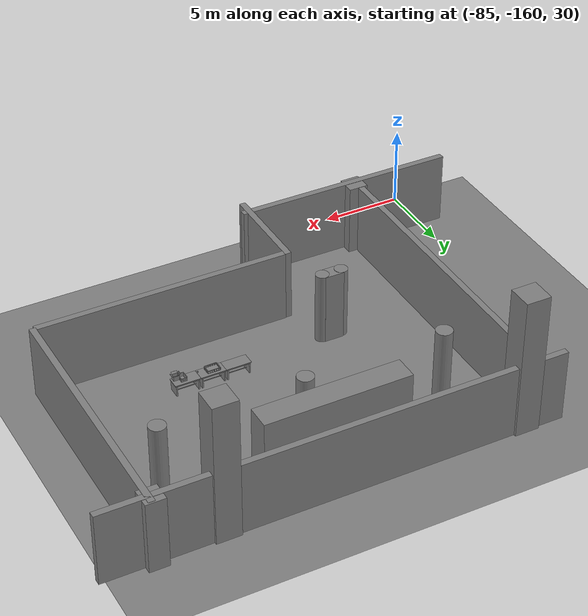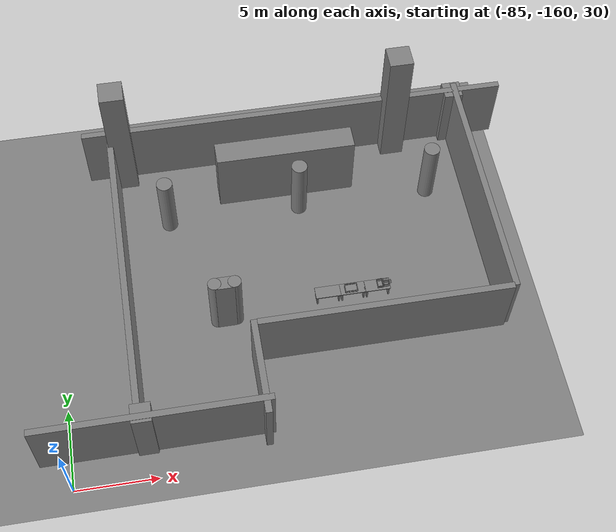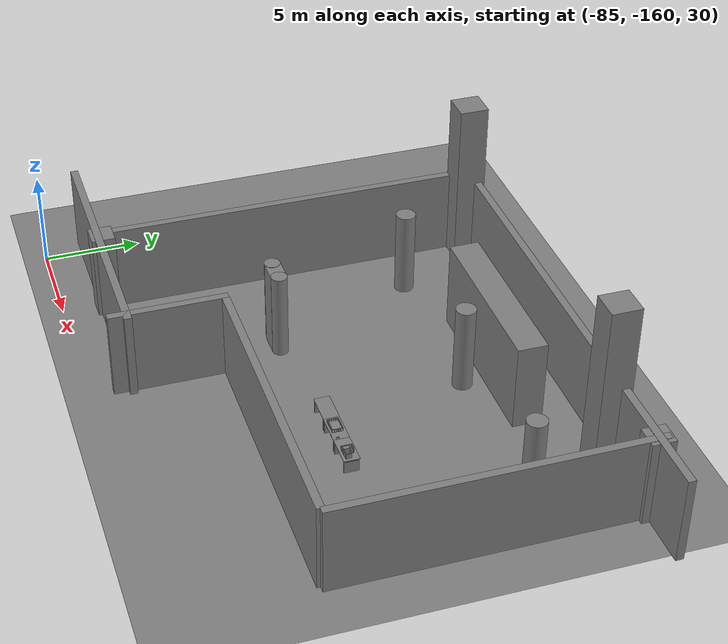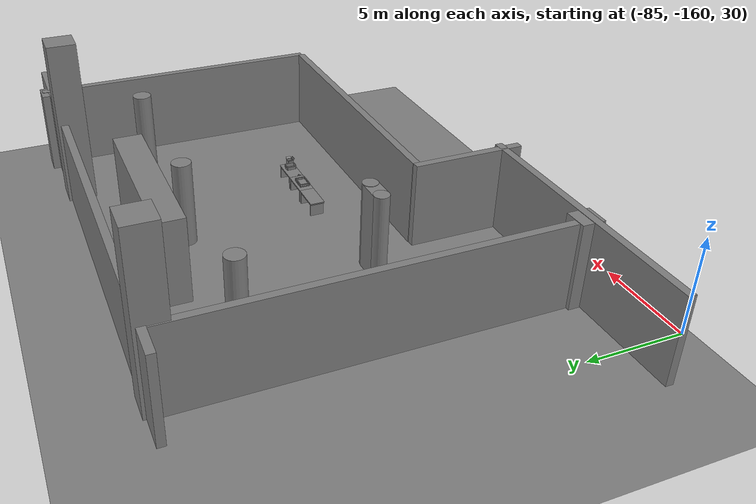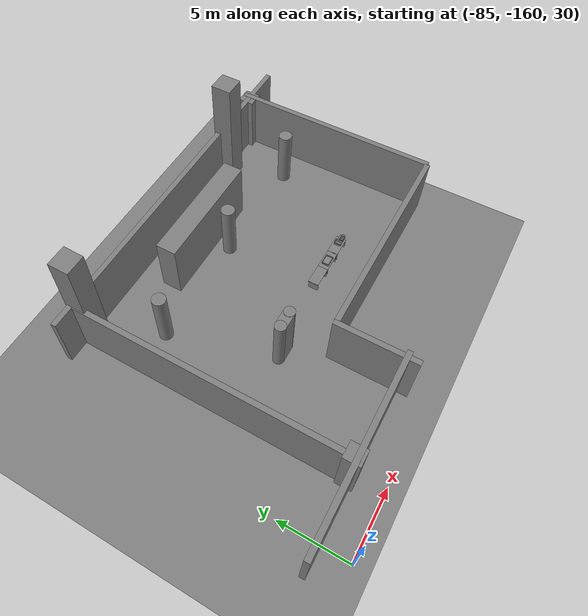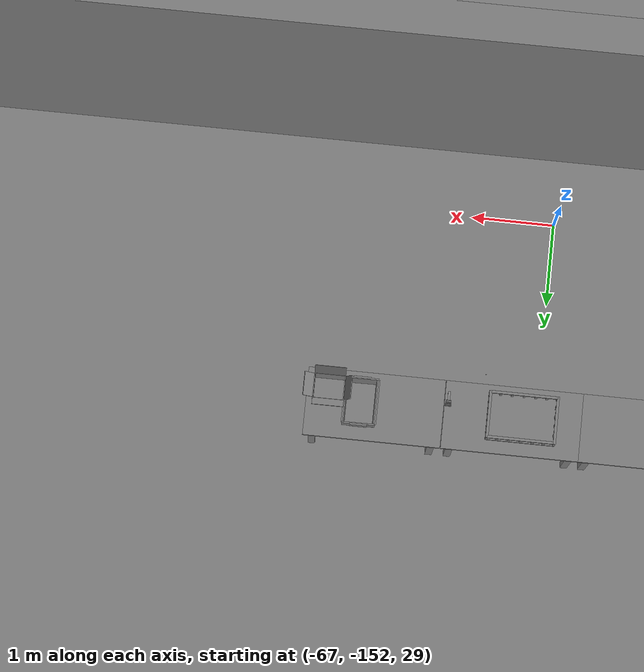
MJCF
<mujoco>
    <option gravity="0.000000000 0.000000000 -9.810000420" timestep="0.0049999999" integrator="implicitfast" density="1.225" viscosity="1.8000001e-05" noslip_iterations="10" iterations="100" sdf_iterations="50">
        <flag multiccd="disable"/>
    </option>
    <size memory="1000M"/>
    <compiler coordinate="local"/>
    <worldbody>
        <light cutoff="30" pos="0 1 1" dir="0 -1 -2"/>
        <light cutoff="30" pos="0 -1 1" dir="0 1 -2"/>
        <body pos="-64.866622925 -149.383972168 30.183746338" euler="89.999992371 89.999946594 0.000000000" name="openloong_gripper_2f85_fix_base_usda_bluebox_01">
            <geom contype="1" conaffinity="1" density="1000" type="box" material="" rgba="0.500000000 0.500000000 0.500000000 1.000000000" solimp="0.899999976 0.949999988 0.001000000" friction="1.000000000 0.005000000 0.000100000" solref="0.020000000 1.000000000" margin="0" condim="3" group="0" pos="0.276596069 0.187225342 0.000061035" quat="0.707107008 0.000077501 0.707106471 0.000077456" size="0.100000001 0.057999998 0.010000000" name="openloong_gripper_2f85_fix_base_usda_geom_3130D857_4881_470B_BF45_2A5D827F5866"/>
            <geom contype="1" conaffinity="1" density="1000" type="box" material="" rgba="0.500000000 0.500000000 0.500000000 1.000000000" solimp="0.899999976 0.949999988 0.001000000" friction="1.000000000 0.005000000 0.000100000" solref="0.020000000 1.000000000" margin="0" condim="3" group="0" pos="0.000000000 0.002883911 0.000000000" quat="1.000000000 0.000000000 0.000000000 0.000000000" size="0.254000008 0.003000000 0.172000006" name="openloong_gripper_2f85_fix_base_usda_geom_41FCDC25_C621_4C34_8C1C_3812BAC6C02C"/>
            <geom contype="1" conaffinity="1" density="1000" type="box" material="" rgba="0.500000000 0.500000000 0.500000000 1.000000000" solimp="0.899999976 0.949999988 0.001000000" friction="1.000000000 0.005000000 0.000100000" solref="0.020000000 1.000000000" margin="0" condim="3" group="0" pos="0.000015259 0.124874115 0.173477173" quat="0.999796450 0.020176515 -0.000000015 0.000000030" size="0.259999990 0.119999997 0.007000000" name="openloong_gripper_2f85_fix_base_usda_geom_2AB21D0D_76FD_43E3_AF3C_F3710FC01021"/>
            <geom contype="1" conaffinity="1" density="1000" type="box" material="" rgba="0.500000000 0.500000000 0.500000000 1.000000000" solimp="0.899999976 0.949999988 0.001000000" friction="1.000000000 0.005000000 0.000100000" solref="0.020000000 1.000000000" margin="0" condim="3" group="0" pos="0.000015259 0.124874115 -0.173477173" quat="0.999796450 -0.020176545 -0.000000015 0.000000000" size="0.259999990 0.119999997 0.007000000" name="openloong_gripper_2f85_fix_base_usda_geom_8208B725_8F25_4583_BC04_C96F558005C8"/>
            <geom contype="1" conaffinity="1" density="1000" type="box" material="" rgba="0.500000000 0.500000000 0.500000000 1.000000000" solimp="0.899999976 0.949999988 0.001000000" friction="1.000000000 0.005000000 0.000100000" solref="0.020000000 1.000000000" margin="0" condim="3" group="0" pos="0.000015259 0.214012146 0.188980103" quat="0.999913096 0.013176724 0.000000015 0.000000000" size="0.259999990 0.029999999 0.012500000" name="openloong_gripper_2f85_fix_base_usda_geom_B9B67454_57C4_464D_830C_8C63FDA5E234"/>
            <geom contype="1" conaffinity="1" density="1000" type="box" material="" rgba="0.500000000 0.500000000 0.500000000 1.000000000" solimp="0.899999976 0.949999988 0.001000000" friction="1.000000000 0.005000000 0.000100000" solref="0.020000000 1.000000000" margin="0" condim="3" group="0" pos="-0.258346558 0.125289917 0.001876831" quat="0.702796996 -0.020792052 0.710783184 0.020769238" size="0.189999998 0.119999997 0.009000000" name="openloong_gripper_2f85_fix_base_usda_geom_8C198B15_2908_4CEB_ABF4_B01190EB4898"/>
            <geom contype="1" conaffinity="1" density="1000" type="box" material="" rgba="0.500000000 0.500000000 0.500000000 1.000000000" solimp="0.899999976 0.949999988 0.001000000" friction="1.000000000 0.005000000 0.000100000" solref="0.020000000 1.000000000" margin="0" condim="3" group="0" pos="0.000015259 0.214012146 -0.188980103" quat="0.999913096 -0.013176769 0.000000030 0.000000015" size="0.259999990 0.029999999 0.012500000" name="openloong_gripper_2f85_fix_base_usda_geom_14E16188_0AC5_41BA_8B6F_091D5B2C5095"/>
            <geom contype="1" conaffinity="1" density="1000" type="box" material="" rgba="0.500000000 0.500000000 0.500000000 1.000000000" solimp="0.899999976 0.949999988 0.001000000" friction="1.000000000 0.005000000 0.000100000" solref="0.020000000 1.000000000" margin="0" condim="3" group="0" pos="-0.276596069 0.187225342 0.000061035" quat="0.707106650 0.000077441 0.707106709 0.000077456" size="0.100000001 0.057999998 0.010000000" name="openloong_gripper_2f85_fix_base_usda_geom_F5FFDD3E_3D2B_42EE_BC7E_0FEBBA9936DD"/>
            <geom contype="1" conaffinity="1" density="1000" type="box" material="" rgba="0.500000000 0.500000000 0.500000000 1.000000000" solimp="0.899999976 0.949999988 0.001000000" friction="1.000000000 0.005000000 0.000100000" solref="0.020000000 1.000000000" margin="0" condim="3" group="0" pos="0.258346558 0.125289917 0.001876831" quat="0.702851534 0.018856451 0.710823834 -0.019329429" size="0.189999998 0.119999997 0.009000000" name="openloong_gripper_2f85_fix_base_usda_geom_C573091E_A9ED_42FD_8841_E5C9C51EEA7C"/>
            <freejoint name="openloong_gripper_2f85_fix_base_usda_bluebox_01_joint"/>
            <site size="0.005000000 0.005000000 0.005000000" rgba="0.500000000 0.500000000 0.500000000 1.000000000" pos="0.000000000 0.000000000 0.000000000" quat="0.999961913 0.008726534 0.000000000 0.000000000" group="0" type="sphere" name="openloong_gripper_2f85_fix_base_usda_bluebox_01site"/>
        </body>
        <body pos="-64.496299744 -149.491867065 30.235729218" euler="0.000000000 0.000000000 89.999946594" name="openloong_gripper_2f85_fix_base_usda_cardboardbox_01">
            <geom contype="1" conaffinity="1" density="1000" type="box" material="" rgba="0.500000000 0.500000000 0.500000000 1.000000000" solimp="0.899999976 0.949999988 0.001000000" friction="1.000000000 0.005000000 0.000100000" solref="0.020000000 1.000000000" margin="0" condim="3" group="0" pos="-0.003166199 -0.004086494 0.005052090" quat="1.000000000 0.000000000 0.000000000 0.000000000" size="0.142499998 0.177500010 0.005000000" name="openloong_gripper_2f85_fix_base_usda_geom_603F253A_0AB4_441C_B0B4_842C9AA4D968"/>
            <geom contype="1" conaffinity="1" density="1000" type="box" material="" rgba="0.500000000 0.500000000 0.500000000 1.000000000" solimp="0.899999976 0.949999988 0.001000000" friction="1.000000000 0.005000000 0.000100000" solref="0.020000000 1.000000000" margin="0" condim="3" group="0" pos="-0.003166199 0.170316696 0.150570869" quat="1.000000000 0.000000000 0.000000000 0.000000000" size="0.142499998 0.005000000 0.149999991" name="openloong_gripper_2f85_fix_base_usda_geom_13F560B2_0835_43A2_B802_4054BD7CF4FC"/>
            <geom contype="1" conaffinity="1" density="1000" type="box" material="" rgba="0.500000000 0.500000000 0.500000000 1.000000000" solimp="0.899999976 0.949999988 0.001000000" friction="1.000000000 0.005000000 0.000100000" solref="0.020000000 1.000000000" margin="0" condim="3" group="0" pos="-0.147399902 -0.005307198 0.150570869" quat="1.000000000 0.000000000 0.000000000 0.000000000" size="0.005000000 0.177500010 0.149999991" name="openloong_gripper_2f85_fix_base_usda_geom_85269EBD_7352_4CBA_B3E5_A9F2A0BB7F7A"/>
            <geom contype="1" conaffinity="1" density="1000" type="box" material="" rgba="0.500000000 0.500000000 0.500000000 1.000000000" solimp="0.899999976 0.949999988 0.001000000" friction="1.000000000 0.005000000 0.000100000" solref="0.020000000 1.000000000" margin="0" condim="3" group="0" pos="0.140275955 -0.005307198 0.150570869" quat="1.000000000 0.000000000 0.000000000 0.000000000" size="0.005000000 0.177500010 0.149999991" name="openloong_gripper_2f85_fix_base_usda_geom_16B72466_9F05_4228_BC0E_3F01C747846C"/>
            <geom contype="1" conaffinity="1" density="1000" type="box" material="" rgba="0.500000000 0.500000000 0.500000000 1.000000000" solimp="0.899999976 0.949999988 0.001000000" friction="1.000000000 0.005000000 0.000100000" solref="0.020000000 1.000000000" margin="0" condim="3" group="0" pos="-0.003166199 -0.181550980 0.150570869" quat="1.000000000 0.000000000 0.000000000 0.000000000" size="0.142499998 0.005000000 0.149999991" name="openloong_gripper_2f85_fix_base_usda_geom_DF5761A5_FFD8_440F_B2D2_B0481BABD8DA"/>
            <freejoint name="openloong_gripper_2f85_fix_base_usda_cardboardbox_01_joint"/>
            <site size="0.005000000 0.005000000 0.005000000" rgba="0.500000000 0.500000000 0.500000000 1.000000000" pos="0.000000000 0.000000000 0.000000000" quat="0.999961913 0.008726535 0.000000000 0.000000000" group="0" type="sphere" name="openloong_gripper_2f85_fix_base_usda_site_067892C8_33F2_42A8_B0B0_03318F7E46BD"/>
            <body pos="0.139160156 -0.004048347 0.301930904" euler="-179.999954224 49.383502960 179.999954224" name="openloong_gripper_2f85_fix_base_usda_A1_006">
                <geom contype="1" conaffinity="1" density="1000" type="box" material="" rgba="0.500000000 0.500000000 0.500000000 1.000000000" solimp="0.899999976 0.949999988 0.001000000" friction="1.000000000 0.005000000 0.000100000" solref="0.020000000 1.000000000" margin="0" condim="3" group="0" pos="-0.071587563 0.000009537 0.001745224" quat="0.999999881 0.000000000 0.000000000 0.000000000" size="0.071249999 0.179999992 0.002500000" name="openloong_gripper_2f85_fix_base_usda_geom_E42A3537_1998_4FEF_BD38_94E608A9DF56"/>
                <joint armature="0" stiffness="0.07" damping="0.0099999998" axis="0.000000 1.000000 0.000000" type="hinge" name="openloong_gripper_2f85_fix_base_usda_A1_006"/>
            </body>
            <body pos="-0.145902634 -0.004086494 0.301938057" euler="-180.000000000 -60.000011444 -180.000000000" name="openloong_gripper_2f85_fix_base_usda_A2_006">
                <geom contype="1" conaffinity="1" density="1000" type="box" material="" rgba="0.500000000 0.500000000 0.500000000 1.000000000" solimp="0.899999976 0.949999988 0.001000000" friction="1.000000000 0.005000000 0.000100000" solref="0.020000000 1.000000000" margin="0" condim="3" group="0" pos="0.071268082 0.000009537 0.002717972" quat="0.000002921 0.000000000 -0.000000030 0.999999881" size="0.071249999 0.179999992 0.002500000" name="openloong_gripper_2f85_fix_base_usda_geom_D3A170BA_BBEA_429A_B197_BD2520D42A34"/>
                <joint armature="0" stiffness="0.07" damping="0.0099999998" axis="0.000000 1.000000 0.000000" type="hinge" name="openloong_gripper_2f85_fix_base_usda_A2_006"/>
            </body>
            <body pos="-0.003385544 0.175991058 0.301930904" euler="-125.858116150 -0.000004561 0.000002331" name="openloong_gripper_2f85_fix_base_usda_B2_006">
                <geom contype="1" conaffinity="1" density="1000" type="box" material="" rgba="0.500000000 0.500000000 0.500000000 1.000000000" solimp="0.899999976 0.949999988 0.001000000" friction="1.000000000 0.005000000 0.000100000" solref="0.020000000 1.000000000" margin="0" condim="3" group="0" pos="0.000009537 -0.070939064 -0.002470016" quat="0.999614120 0.027776197 -0.000000015 0.000000030" size="0.137500003 0.064999998 0.005000000" name="openloong_gripper_2f85_fix_base_usda_geom_ED2CDAA9_B211_4396_9B73_88517D800694"/>
                <joint armature="0" stiffness="0.07" damping="0.0099999998" axis="1.000000 0.000000 0.000000" type="hinge" name="openloong_gripper_2f85_fix_base_usda_B2_006"/>
            </body>
            <body pos="-0.003385544 -0.184140205 0.301938057" euler="147.805557251 0.000000000 0.000000000" name="openloong_gripper_2f85_fix_base_usda_B1_006">
                <geom contype="1" conaffinity="1" density="1000" type="box" material="" rgba="0.500000000 0.500000000 0.500000000 1.000000000" solimp="0.899999976 0.949999988 0.001000000" friction="1.000000000 0.005000000 0.000100000" solref="0.020000000 1.000000000" margin="0" condim="3" group="0" pos="-0.000028610 0.070202351 -0.002703667" quat="0.999614179 -0.027776167 0.000000000 0.000000000" size="0.137500003 0.064999998 0.005000000" name="openloong_gripper_2f85_fix_base_usda_geom_A31E7026_EF38_410A_B1ED_3954A4B43950"/>
                <joint armature="0" stiffness="0.07" damping="0.0099999998" axis="1.000000 0.000000 0.000000" type="hinge" name="openloong_gripper_2f85_fix_base_usda_B1_006"/>
            </body>
        </body>
        <body pos="-65.882858276 -149.481979370 30.229999542" euler="-64.487716675 0.000000000 0.000000000" name="openloong_gripper_2f85_fix_base_usda_Barcode">
            <geom contype="1" conaffinity="1" density="1000" type="box" material="" rgba="0.500000000 0.500000000 0.500000000 1.000000000" solimp="0.899999976 0.949999988 0.001000000" friction="1.000000000 0.005000000 0.000100000" solref="0.020000000 1.000000000" margin="0" condim="3" group="0" pos="0.000000000 0.013038635 0.001419067" quat="0.000000000 0.000000000 0.000000000 1.000000119" size="0.034000002 0.010000000 0.017999999" name="openloong_gripper_2f85_fix_base_usda_geom_4808B75E_C557_418D_AC46_04710B3BBEBD"/>
            <geom contype="1" conaffinity="1" density="1000" type="box" material="" rgba="0.500000000 0.500000000 0.500000000 1.000000000" solimp="0.899999976 0.949999988 0.001000000" friction="1.000000000 0.005000000 0.000100000" solref="0.020000000 1.000000000" margin="0" condim="3" group="0" pos="0.000000000 -0.035301208 -0.007095337" quat="0.000000000 0.000000000 -0.043619365 0.999048233" size="0.028999999 0.010000000 0.020000000" name="openloong_gripper_2f85_fix_base_usda_geom_D262582A_3BA0_453D_B1AA_2DAB3C15A852"/>
            <geom contype="1" conaffinity="1" density="1000" type="box" material="" rgba="0.500000000 0.500000000 0.500000000 1.000000000" solimp="0.899999976 0.949999988 0.001000000" friction="1.000000000 0.005000000 0.000100000" solref="0.020000000 1.000000000" margin="0" condim="3" group="0" pos="0.000000000 -0.043411255 -0.011749268" quat="0.922262907 0.386563420 0.000000000 0.000000000" size="0.026000001 0.010000000 0.020000000" name="openloong_gripper_2f85_fix_base_usda_geom_E6246CA5_3014_4C17_9927_1A41B53E2BE7"/>
            <geom contype="1" conaffinity="1" density="1000" type="box" material="" rgba="0.500000000 0.500000000 0.500000000 1.000000000" solimp="0.899999976 0.949999988 0.001000000" friction="1.000000000 0.005000000 0.000100000" solref="0.020000000 1.000000000" margin="0" condim="3" group="0" pos="0.000000000 -0.016967773 -0.031860352" quat="0.000000000 0.000000000 0.000000000 1.000000119" size="0.008000000 0.010000000 0.013000000" name="openloong_gripper_2f85_fix_base_usda_geom_6389FD78_17CA_4134_A5E9_396CBD29CE78"/>
            <geom contype="1" conaffinity="1" density="1000" type="box" material="" rgba="0.500000000 0.500000000 0.500000000 1.000000000" solimp="0.899999976 0.949999988 0.001000000" friction="1.000000000 0.005000000 0.000100000" solref="0.020000000 1.000000000" margin="0" condim="3" group="0" pos="0.000000000 -0.001869202 0.000312805" quat="0.953716993 0.300705761 0.000000000 0.000000000" size="0.032000002 0.010000000 0.018999999" name="openloong_gripper_2f85_fix_base_usda_geom_15655933_EA2C_4564_82DB_72FC1BB8F77D"/>
            <geom contype="1" conaffinity="1" density="1000" type="box" material="" rgba="0.500000000 0.500000000 0.500000000 1.000000000" solimp="0.899999976 0.949999988 0.001000000" friction="1.000000000 0.005000000 0.000100000" solref="0.020000000 1.000000000" margin="0" condim="3" group="0" pos="0.000000000 -0.019531250 -0.003173828" quat="0.953716993 0.300705761 0.000000000 0.000000000" size="0.030999999 0.010000000 0.020000000" name="openloong_gripper_2f85_fix_base_usda_geom_816CED7A_E558_46A8_ACA9_A27B30ACB21E"/>
            <geom contype="1" conaffinity="1" density="1000" type="box" material="" rgba="0.500000000 0.500000000 0.500000000 1.000000000" solimp="0.899999976 0.949999988 0.001000000" friction="1.000000000 0.005000000 0.000100000" solref="0.020000000 1.000000000" margin="0" condim="3" group="0" pos="0.000000000 -0.035301208 -0.007095337" quat="0.953716993 0.300705761 0.000000000 0.000000000" size="0.028999999 0.010000000 0.020000000" name="openloong_gripper_2f85_fix_base_usda_geom_78C58902_78B0_48DD_9F24_A92AFB48FA6A"/>
            <geom contype="1" conaffinity="1" density="1000" type="box" material="" rgba="0.500000000 0.500000000 0.500000000 1.000000000" solimp="0.899999976 0.949999988 0.001000000" friction="1.000000000 0.005000000 0.000100000" solref="0.020000000 1.000000000" margin="0" condim="3" group="0" pos="0.000000000 -0.042617798 -0.071121216" quat="0.000000000 0.000000000 0.000000000 1.000000119" size="0.013000000 0.021000000 0.059999999" name="openloong_gripper_2f85_fix_base_usda_geom_94E6FF71_9018_4CFA_B676_B57D16DFC7FF"/>
            <freejoint name="openloong_gripper_2f85_fix_base_usda_Barcode_joint"/>
            <site size="0.005000000 0.005000000 0.005000000" rgba="0.500000000 0.500000000 0.500000000 1.000000000" pos="0.000000000 0.000000000 0.000000000" quat="1.000000000 0.000000000 0.000000000 0.000000000" group="0" type="sphere" name="openloong_gripper_2f85_fix_base_usda_Barcode_site"/>
        </body>
        <body pos="-66.745018005 -149.392349243 30.184000015" euler="0.000000000 0.000000000 89.999946594" name="[22331881980903]_Basket_01">
            <geom contype="1" conaffinity="1" density="1000" type="box" material="" rgba="0.500000000 0.500000000 0.500000000 1.000000000" solimp="0.899999976 0.949999988 0.001000000" friction="1.000000000 0.005000000 0.000100000" solref="0.020000000 1.000000000" margin="0" condim="3" group="0" pos="-0.052425385 0.389207840 0.089787483" quat="0.707107008 0.000000000 0.000000000 0.707106411" size="0.014249999 0.014249999 0.059999999" name="[22331881980903]_geom_70DB02F2_CCC3_4919_A71B_7A3244CB7DBF"/>
            <geom contype="1" conaffinity="1" density="1000" type="box" material="" rgba="0.500000000 0.500000000 0.500000000 1.000000000" solimp="0.899999976 0.949999988 0.001000000" friction="1.000000000 0.005000000 0.000100000" solref="0.020000000 1.000000000" margin="0" condim="3" group="0" pos="0.264015198 -0.133043289 0.089787483" quat="0.707107008 0.000000000 0.000000000 0.707106411" size="0.014249999 0.014249999 0.059999999" name="[22331881980903]_geom_3C1D40EE_2F04_4F7C_B4FE_D905BB5D3492"/>
            <geom contype="1" conaffinity="1" density="1000" type="box" material="" rgba="0.500000000 0.500000000 0.500000000 1.000000000" solimp="0.899999976 0.949999988 0.001000000" friction="1.000000000 0.005000000 0.000100000" solref="0.020000000 1.000000000" margin="0" condim="3" group="0" pos="-0.264015198 -0.265548706 0.089793205" quat="0.707107008 0.000000000 0.000000000 0.707106411" size="0.014249999 0.014249999 0.059999999" name="[22331881980903]_geom_DBE95549_02EB_4E16_8C22_79FB65E3578A"/>
            <geom contype="1" conaffinity="1" density="1000" type="box" material="" rgba="0.500000000 0.500000000 0.500000000 1.000000000" solimp="0.899999976 0.949999988 0.001000000" friction="1.000000000 0.005000000 0.000100000" solref="0.020000000 1.000000000" margin="0" condim="3" group="0" pos="-0.160263062 -0.389322281 0.089793205" quat="0.707107008 0.000000000 0.000000000 0.707106411" size="0.014249999 0.014249999 0.059999999" name="[22331881980903]_geom_C5733433_F1BA_4BF1_9343_B1B49DE3C940"/>
            <geom contype="1" conaffinity="1" density="1000" type="box" material="" rgba="0.500000000 0.500000000 0.500000000 1.000000000" solimp="0.899999976 0.949999988 0.001000000" friction="1.000000000 0.005000000 0.000100000" solref="0.020000000 1.000000000" margin="0" condim="3" group="0" pos="0.162265778 -0.389322281 0.089787483" quat="0.707107008 0.000000000 0.000000000 0.707106411" size="0.014249999 0.014249999 0.059999999" name="[22331881980903]_geom_567488BA_C166_41B8_BB89_964F6762EA1B"/>
            <geom contype="1" conaffinity="1" density="1000" type="box" material="" rgba="0.500000000 0.500000000 0.500000000 1.000000000" solimp="0.899999976 0.949999988 0.001000000" friction="1.000000000 0.005000000 0.000100000" solref="0.020000000 1.000000000" margin="0" condim="3" group="0" pos="0.264015198 0.389207840 0.089787483" quat="0.707107008 0.000000000 0.000000000 0.707106411" size="0.014249999 0.014249999 0.059999999" name="[22331881980903]_geom_F3A197C6_E0E6_43EA_866C_8283CAA5EE1B"/>
            <geom contype="1" conaffinity="1" density="1000" type="box" material="" rgba="0.500000000 0.500000000 0.500000000 1.000000000" solimp="0.899999976 0.949999988 0.001000000" friction="1.000000000 0.005000000 0.000100000" solref="0.020000000 1.000000000" margin="0" condim="3" group="0" pos="-0.264015198 -0.133043289 0.089793205" quat="0.707107008 0.000000000 0.000000000 0.707106411" size="0.014249999 0.014249999 0.059999999" name="[22331881980903]_geom_027DA1CA_26DE_426E_8639_D5F7B467A5AE"/>
            <geom contype="1" conaffinity="1" density="1000" type="box" material="" rgba="0.500000000 0.500000000 0.500000000 1.000000000" solimp="0.899999976 0.949999988 0.001000000" friction="1.000000000 0.005000000 0.000100000" solref="0.020000000 1.000000000" margin="0" condim="3" group="0" pos="-0.264026642 0.269256592 0.089793205" quat="0.707107008 0.000000000 0.000000000 0.707106411" size="0.014249999 0.014249999 0.059999999" name="[22331881980903]_geom_3349097C_FA72_4A15_B6EB_3E11A6EB82AB"/>
            <geom contype="1" conaffinity="1" density="1000" type="box" material="" rgba="0.500000000 0.500000000 0.500000000 1.000000000" solimp="0.899999976 0.949999988 0.001000000" friction="1.000000000 0.005000000 0.000100000" solref="0.020000000 1.000000000" margin="0" condim="3" group="0" pos="0.054462433 0.389207840 0.089787483" quat="0.707107008 0.000000000 0.000000000 0.707106411" size="0.014249999 0.014249999 0.059999999" name="[22331881980903]_geom_A5FFEA65_95AD_46B2_9931_26C7D3674900"/>
            <geom contype="1" conaffinity="1" density="1000" type="box" material="" rgba="0.500000000 0.500000000 0.500000000 1.000000000" solimp="0.899999976 0.949999988 0.001000000" friction="1.000000000 0.005000000 0.000100000" solref="0.020000000 1.000000000" margin="0" condim="3" group="0" pos="0.054462433 -0.389322281 0.089787483" quat="0.707107008 0.000000000 0.000000000 0.707106411" size="0.014249999 0.014249999 0.059999999" name="[22331881980903]_geom_F59170AF_A436_43D4_901C_B7B21FB061AF"/>
            <geom contype="1" conaffinity="1" density="1000" type="box" material="" rgba="0.500000000 0.500000000 0.500000000 1.000000000" solimp="0.899999976 0.949999988 0.001000000" friction="1.000000000 0.005000000 0.000100000" solref="0.020000000 1.000000000" margin="0" condim="3" group="0" pos="0.264015198 0.269256592 0.089793205" quat="0.707107008 0.000000000 0.000000000 0.707106411" size="0.014249999 0.014249999 0.059999999" name="[22331881980903]_geom_D05F3627_4A73_40E0_B79D_E40475170565"/>
            <geom contype="1" conaffinity="1" density="1000" type="box" material="" rgba="0.500000000 0.500000000 0.500000000 1.000000000" solimp="0.899999976 0.949999988 0.001000000" friction="1.000000000 0.005000000 0.000100000" solref="0.020000000 1.000000000" margin="0" condim="3" group="0" pos="0.264015198 -0.389322281 0.089787483" quat="0.707107008 0.000000000 0.000000000 0.707106411" size="0.014249999 0.014249999 0.059999999" name="[22331881980903]_geom_82522111_E362_4C5A_842F_2A07377354F1"/>
            <geom contype="1" conaffinity="1" density="1000" type="box" material="" rgba="0.500000000 0.500000000 0.500000000 1.000000000" solimp="0.899999976 0.949999988 0.001000000" friction="1.000000000 0.005000000 0.000100000" solref="0.020000000 1.000000000" margin="0" condim="3" group="0" pos="0.000000000 0.000000000 0.015998840" quat="0.707107008 0.000000000 0.000000000 0.707106411" size="0.403499991 0.279000014 0.015750000" name="[22331881980903]_geom_832167A6_9C21_4B0B_9A52_4F4C0228BC22"/>
            <geom contype="1" conaffinity="1" density="1000" type="box" material="" rgba="0.500000000 0.500000000 0.500000000 1.000000000" solimp="0.899999976 0.949999988 0.001000000" friction="1.000000000 0.005000000 0.000100000" solref="0.020000000 1.000000000" margin="0" condim="3" group="0" pos="0.000000000 -0.389476776 0.163619041" quat="0.707107008 0.000000000 0.000000000 0.707106411" size="0.015000000 0.277500004 0.015750000" name="[22331881980903]_geom_CA898D48_3B5A_499E_9A6E_D494681113C6"/>
            <geom contype="1" conaffinity="1" density="1000" type="box" material="" rgba="0.500000000 0.500000000 0.500000000 1.000000000" solimp="0.899999976 0.949999988 0.001000000" friction="1.000000000 0.005000000 0.000100000" solref="0.020000000 1.000000000" margin="0" condim="3" group="0" pos="0.162265778 0.389207840 0.089787483" quat="0.707107008 0.000000000 0.000000000 0.707106411" size="0.014249999 0.014249999 0.059999999" name="[22331881980903]_geom_07479E6A_6490_4E55_A8D5_284EF5F1F009"/>
            <geom contype="1" conaffinity="1" density="1000" type="box" material="" rgba="0.500000000 0.500000000 0.500000000 1.000000000" solimp="0.899999976 0.949999988 0.001000000" friction="1.000000000 0.005000000 0.000100000" solref="0.020000000 1.000000000" margin="0" condim="3" group="0" pos="0.000000000 0.389471054 0.163619041" quat="0.707107008 0.000000000 0.000000000 0.707106411" size="0.015000000 0.277500004 0.015750000" name="[22331881980903]_geom_CAD48F9D_F00C_4588_A8C5_311A354318FC"/>
            <geom contype="1" conaffinity="1" density="1000" type="box" material="" rgba="0.500000000 0.500000000 0.500000000 1.000000000" solimp="0.899999976 0.949999988 0.001000000" friction="1.000000000 0.005000000 0.000100000" solref="0.020000000 1.000000000" margin="0" condim="3" group="0" pos="-0.263511658 0.000000000 0.163619041" quat="0.707107008 0.000000000 0.000000000 0.707106411" size="0.403499991 0.015000000 0.015750000" name="[22331881980903]_geom_A69E9014_46C9_4397_9B68_7150F1666E16"/>
            <geom contype="1" conaffinity="1" density="1000" type="box" material="" rgba="0.500000000 0.500000000 0.500000000 1.000000000" solimp="0.899999976 0.949999988 0.001000000" friction="1.000000000 0.005000000 0.000100000" solref="0.020000000 1.000000000" margin="0" condim="3" group="0" pos="-0.264015198 0.141334534 0.089793205" quat="0.707107008 0.000000000 0.000000000 0.707106411" size="0.014249999 0.014249999 0.059999999" name="[22331881980903]_geom_FB72AF40_5F79_4201_9964_D452125AF636"/>
            <geom contype="1" conaffinity="1" density="1000" type="box" material="" rgba="0.500000000 0.500000000 0.500000000 1.000000000" solimp="0.899999976 0.949999988 0.001000000" friction="1.000000000 0.005000000 0.000100000" solref="0.020000000 1.000000000" margin="0" condim="3" group="0" pos="0.264015198 -0.265548706 0.089787483" quat="0.707107008 0.000000000 0.000000000 0.707106411" size="0.014249999 0.014249999 0.059999999" name="[22331881980903]_geom_1493949A_B5AC_4CE7_96E8_A77D4FDAC4DC"/>
            <geom contype="1" conaffinity="1" density="1000" type="box" material="" rgba="0.500000000 0.500000000 0.500000000 1.000000000" solimp="0.899999976 0.949999988 0.001000000" friction="1.000000000 0.005000000 0.000100000" solref="0.020000000 1.000000000" margin="0" condim="3" group="0" pos="-0.160263062 0.389207840 0.089787483" quat="0.707107008 0.000000000 0.000000000 0.707106411" size="0.014249999 0.014249999 0.059999999" name="[22331881980903]_geom_8554A949_5EDD_40BA_8FCE_FB72A2DD2316"/>
            <geom contype="1" conaffinity="1" density="1000" type="box" material="" rgba="0.500000000 0.500000000 0.500000000 1.000000000" solimp="0.899999976 0.949999988 0.001000000" friction="1.000000000 0.005000000 0.000100000" solref="0.020000000 1.000000000" margin="0" condim="3" group="0" pos="-0.052425385 -0.389322281 0.089787483" quat="0.707107008 0.000000000 0.000000000 0.707106411" size="0.014249999 0.014249999 0.059999999" name="[22331881980903]_geom_E1C41FA4_7835_445C_A666_98A6711D28D4"/>
            <geom contype="1" conaffinity="1" density="1000" type="box" material="" rgba="0.500000000 0.500000000 0.500000000 1.000000000" solimp="0.899999976 0.949999988 0.001000000" friction="1.000000000 0.005000000 0.000100000" solref="0.020000000 1.000000000" margin="0" condim="3" group="0" pos="-0.264026642 -0.389322281 0.089793205" quat="0.707107008 0.000000000 0.000000000 0.707106411" size="0.014249999 0.014249999 0.059999999" name="[22331881980903]_geom_50B4C952_5111_4A97_A980_C3DA05A54FFF"/>
            <geom contype="1" conaffinity="1" density="1000" type="box" material="" rgba="0.500000000 0.500000000 0.500000000 1.000000000" solimp="0.899999976 0.949999988 0.001000000" friction="1.000000000 0.005000000 0.000100000" solref="0.020000000 1.000000000" margin="0" condim="3" group="0" pos="0.264015198 0.141334534 0.089787483" quat="0.707107008 0.000000000 0.000000000 0.707106411" size="0.014249999 0.014249999 0.059999999" name="[22331881980903]_geom_BD5250BA_8244_4893_B598_7028C574B259"/>
            <geom contype="1" conaffinity="1" density="1000" type="box" material="" rgba="0.500000000 0.500000000 0.500000000 1.000000000" solimp="0.899999976 0.949999988 0.001000000" friction="1.000000000 0.005000000 0.000100000" solref="0.020000000 1.000000000" margin="0" condim="3" group="0" pos="-0.264015198 0.389207840 0.089793205" quat="0.707107008 0.000000000 0.000000000 0.707106411" size="0.014249999 0.014249999 0.059999999" name="[22331881980903]_geom_CD1165A7_D52E_44E8_8FB3_DAFC97EBCC7A"/>
            <geom contype="1" conaffinity="1" density="1000" type="box" material="" rgba="0.500000000 0.500000000 0.500000000 1.000000000" solimp="0.899999976 0.949999988 0.001000000" friction="1.000000000 0.005000000 0.000100000" solref="0.020000000 1.000000000" margin="0" condim="3" group="0" pos="0.264015198 0.004480362 0.089787483" quat="0.707107008 0.000000000 0.000000000 0.707106411" size="0.014249999 0.014249999 0.059999999" name="[22331881980903]_geom_011EFB0A_6BC2_42A9_A59B_0739C456E07E"/>
            <geom contype="1" conaffinity="1" density="1000" type="box" material="" rgba="0.500000000 0.500000000 0.500000000 1.000000000" solimp="0.899999976 0.949999988 0.001000000" friction="1.000000000 0.005000000 0.000100000" solref="0.020000000 1.000000000" margin="0" condim="3" group="0" pos="0.263694763 -0.000011444 0.163619041" quat="0.707107008 0.000000000 0.000000000 0.707106411" size="0.403499991 0.015000000 0.015750000" name="[22331881980903]_geom_38BEB68A_6448_4285_82D1_CF1A7C99C5A5"/>
            <geom contype="1" conaffinity="1" density="1000" type="box" material="" rgba="0.500000000 0.500000000 0.500000000 1.000000000" solimp="0.899999976 0.949999988 0.001000000" friction="1.000000000 0.005000000 0.000100000" solref="0.020000000 1.000000000" margin="0" condim="3" group="0" pos="-0.264015198 0.004480362 0.089793205" quat="0.707107008 0.000000000 0.000000000 0.707106411" size="0.014249999 0.014249999 0.059999999" name="[22331881980903]_geom_F2C4D40F_FD14_49C2_A1A4_3406F0B81450"/>
            <freejoint name="[22331881980903]_joint_6628CE09_856F_4D69_9AC8_16EB31D33C3A"/>
        </body>
        <body pos="0.000000000 0.000000000 0.000000000" euler="0.000000000 0.000000000 0.000000000" name="Static Objects_Static Objects">
            <geom contype="1" conaffinity="1" density="1000" type="box" material="" rgba="0.500000000 0.500000000 0.500000000 1.000000000" solimp="0.899999976 0.949999988 0.001000000" friction="1.000000000 0.005000000 0.000100000" solref="0.020000000 1.000000000" margin="0" condim="3" group="0" pos="-67.544113159 -149.365814209 29.727830887" quat="0.500000417 0.499999970 0.499999553 0.499999970" size="0.381000012 0.319999993 0.041000001" name="Static Objects_geom_3D0CE444_3C3A_483D_A55E_1B76C68CAB77"/>
            <geom contype="1" conaffinity="1" density="1000" type="box" material="" rgba="0.500000000 0.500000000 0.500000000 1.000000000" solimp="0.899999976 0.949999988 0.001000000" friction="1.000000000 0.005000000 0.000100000" solref="0.020000000 1.000000000" margin="0" condim="3" group="0" pos="-68.239501953 -149.365814209 30.086868286" quat="0.500000417 0.499999970 0.499999553 0.499999970" size="0.370999992 0.039500002 0.745000005" name="Static Objects_geom_C9AE7919_9E81_4CED_B731_7E3C7E89D36E"/>
            <geom contype="1" conaffinity="1" density="1000" type="box" material="" rgba="0.500000000 0.500000000 0.500000000 1.000000000" solimp="0.899999976 0.949999988 0.001000000" friction="1.000000000 0.005000000 0.000100000" solref="0.020000000 1.000000000" margin="0" condim="3" group="0" pos="-68.239501953 -149.365814209 30.147235870" quat="0.500000417 0.499999970 0.499999553 0.499999970" size="0.400000006 0.022000000 0.800000012" name="Static Objects_geom_98449BF5_25EC_42DB_AB00_2F10D9A8F1D1"/>
            <geom contype="1" conaffinity="1" density="1000" type="box" material="" rgba="0.500000000 0.500000000 0.500000000 1.000000000" solimp="0.899999976 0.949999988 0.001000000" friction="1.000000000 0.005000000 0.000100000" solref="0.020000000 1.000000000" margin="0" condim="3" group="0" pos="-68.934890747 -149.365814209 29.727830887" quat="0.500000417 0.499999970 0.499999553 0.499999970" size="0.381000012 0.319999993 0.041000001" name="Static Objects_geom_1C95649F_00A8_4F24_BF4B_C60ABBFA3066"/>
            <geom contype="1" conaffinity="1" density="1000" type="box" material="" rgba="0.500000000 0.500000000 0.500000000 1.000000000" solimp="0.899999976 0.949999988 0.001000000" friction="1.000000000 0.005000000 0.000100000" solref="0.020000000 1.000000000" margin="0" condim="3" group="0" pos="-68.239501953 -149.365814209 29.561563492" quat="0.500000417 0.499999970 0.499999553 0.499999970" size="0.020000000 0.022000000 0.660000026" name="Static Objects_geom_92AB6D46_FC64_45F3_8393_D1F55679928B"/>
            <geom contype="1" conaffinity="1" density="1000" type="box" material="" rgba="0.500000000 0.500000000 0.500000000 1.000000000" solimp="0.899999976 0.949999988 0.001000000" friction="1.000000000 0.005000000 0.000100000" solref="0.020000000 1.000000000" margin="0" condim="3" group="0" pos="-65.945671082 -149.365814209 29.727830887" quat="0.500000417 0.499999970 0.499999553 0.499999970" size="0.381000012 0.319999993 0.041000001" name="Static Objects_geom_F4E60503_025F_48FE_BA7C_BA8391E8640C"/>
            <geom contype="1" conaffinity="1" density="1000" type="box" material="" rgba="0.500000000 0.500000000 0.500000000 1.000000000" solimp="0.899999976 0.949999988 0.001000000" friction="1.000000000 0.005000000 0.000100000" solref="0.020000000 1.000000000" margin="0" condim="3" group="0" pos="-66.641059875 -149.365814209 30.086868286" quat="0.500000417 0.499999970 0.499999553 0.499999970" size="0.370999992 0.039500002 0.745000005" name="Static Objects_geom_290B103A_75C6_40AF_93BE_AE803AB362D8"/>
            <geom contype="1" conaffinity="1" density="1000" type="box" material="" rgba="0.500000000 0.500000000 0.500000000 1.000000000" solimp="0.899999976 0.949999988 0.001000000" friction="1.000000000 0.005000000 0.000100000" solref="0.020000000 1.000000000" margin="0" condim="3" group="0" pos="-66.641059875 -149.365814209 30.147235870" quat="0.500000417 0.499999970 0.499999553 0.499999970" size="0.400000006 0.022000000 0.800000012" name="Static Objects_geom_D7F08263_3308_475E_B9E4_CEA140D25620"/>
            <geom contype="1" conaffinity="1" density="1000" type="box" material="" rgba="0.500000000 0.500000000 0.500000000 1.000000000" solimp="0.899999976 0.949999988 0.001000000" friction="1.000000000 0.005000000 0.000100000" solref="0.020000000 1.000000000" margin="0" condim="3" group="0" pos="-67.336448669 -149.365814209 29.727830887" quat="0.500000417 0.499999970 0.499999553 0.499999970" size="0.381000012 0.319999993 0.041000001" name="Static Objects_geom_289A565A_81AA_4288_9E51_6198A290CDCA"/>
            <geom contype="1" conaffinity="1" density="1000" type="box" material="" rgba="0.500000000 0.500000000 0.500000000 1.000000000" solimp="0.899999976 0.949999988 0.001000000" friction="1.000000000 0.005000000 0.000100000" solref="0.020000000 1.000000000" margin="0" condim="3" group="0" pos="-66.641059875 -149.365814209 29.561563492" quat="0.500000417 0.499999970 0.499999553 0.499999970" size="0.020000000 0.022000000 0.660000026" name="Static Objects_geom_4298D0A5_153A_4B3C_B1EF_A92FB5C6A731"/>
            <geom contype="1" conaffinity="1" density="1000" type="box" material="" rgba="0.500000000 0.500000000 0.500000000 1.000000000" solimp="0.899999976 0.949999988 0.001000000" friction="1.000000000 0.005000000 0.000100000" solref="0.020000000 1.000000000" margin="0" condim="3" group="0" pos="-64.338577271 -149.365814209 29.727830887" quat="0.500000417 0.499999970 0.499999553 0.499999970" size="0.381000012 0.319999993 0.041000001" name="Static Objects_geom_9F9AC1FD_7A7E_49C8_BF04_FDC9E16949F0"/>
            <geom contype="1" conaffinity="1" density="1000" type="box" material="" rgba="0.500000000 0.500000000 0.500000000 1.000000000" solimp="0.899999976 0.949999988 0.001000000" friction="1.000000000 0.005000000 0.000100000" solref="0.020000000 1.000000000" margin="0" condim="3" group="0" pos="-65.033966064 -149.365814209 30.086868286" quat="0.500000417 0.499999970 0.499999553 0.499999970" size="0.370999992 0.039500002 0.745000005" name="Static Objects_geom_20181CFA_D6FB_49B2_9C50_53C0CFB3DB57"/>
            <geom contype="1" conaffinity="1" density="1000" type="box" material="" rgba="0.500000000 0.500000000 0.500000000 1.000000000" solimp="0.899999976 0.949999988 0.001000000" friction="1.000000000 0.005000000 0.000100000" solref="0.020000000 1.000000000" margin="0" condim="3" group="0" pos="-65.033966064 -149.365814209 30.147235870" quat="0.500000417 0.499999970 0.499999553 0.499999970" size="0.400000006 0.022000000 0.800000012" name="Static Objects_geom_99ECFC67_9F1E_4949_BA97_C98A2DE884B8"/>
            <geom contype="1" conaffinity="1" density="1000" type="box" material="" rgba="0.500000000 0.500000000 0.500000000 1.000000000" solimp="0.899999976 0.949999988 0.001000000" friction="1.000000000 0.005000000 0.000100000" solref="0.020000000 1.000000000" margin="0" condim="3" group="0" pos="-65.729354858 -149.365814209 29.727830887" quat="0.500000417 0.499999970 0.499999553 0.499999970" size="0.381000012 0.319999993 0.041000001" name="Static Objects_geom_CB1D6E0E_CE25_4CBA_963F_7A480F184784"/>
            <geom contype="1" conaffinity="1" density="1000" type="box" material="" rgba="0.500000000 0.500000000 0.500000000 1.000000000" solimp="0.899999976 0.949999988 0.001000000" friction="1.000000000 0.005000000 0.000100000" solref="0.020000000 1.000000000" margin="0" condim="3" group="0" pos="-65.033966064 -149.365814209 29.561563492" quat="0.500000417 0.499999970 0.499999553 0.499999970" size="0.020000000 0.022000000 0.660000026" name="Static Objects_geom_929ED149_E501_43E8_BF65_9E56178E1A71"/>
            <geom contype="1" conaffinity="1" density="1000" type="box" material="" rgba="0.500000000 0.500000000 0.500000000 1.000000000" solimp="0.899999976 0.949999988 0.001000000" friction="1.000000000 0.005000000 0.000100000" solref="0.020000000 1.000000000" margin="0" condim="3" group="0" pos="-61.754566193 -137.853729248 33.906845093" quat="0.707107067 0.000000000 0.000000000 0.707106471" size="0.759999990 0.759999990 4.500000000" name="Static Objects_geom_A1C27E92_C51A_4BC3_8323_5BD0AF97A7A3"/>
            <geom contype="1" conaffinity="1" density="1000" type="box" material="" rgba="0.500000000 0.500000000 0.500000000 1.000000000" solimp="0.899999976 0.949999988 0.001000000" friction="1.000000000 0.005000000 0.000100000" solref="0.020000000 1.000000000" margin="0" condim="3" group="0" pos="-57.511135101 -144.927108765 31.707921982" quat="1.000000000 0.000000000 0.000000000 0.000000000" size="0.200000003 8.000000000 2.299999952" name="Static Objects_geom_CA296D63_D730_4F84_9DAB_61CBCA9A97F8"/>
            <geom contype="1" conaffinity="1" density="1000" type="box" material="" rgba="0.500000000 0.500000000 0.500000000 1.000000000" solimp="0.899999976 0.949999988 0.001000000" friction="1.000000000 0.005000000 0.000100000" solref="0.020000000 1.000000000" margin="0" condim="3" group="0" pos="-80.517646790 -157.574050903 31.688196182" quat="0.707107067 0.000000000 0.000000000 0.707106471" size="0.600000024 0.600000024 2.299999952" name="Static Objects_geom_ED274A50_7A7B_4AFB_B285_774F98E021B2"/>
            <geom contype="1" conaffinity="1" density="1000" type="box" material="" rgba="0.500000000 0.500000000 0.500000000 1.000000000" solimp="0.899999976 0.949999988 0.001000000" friction="1.000000000 0.005000000 0.000100000" solref="0.020000000 1.000000000" margin="0" condim="3" group="0" pos="-80.711044312 -147.414932251 31.666158676" quat="1.000000000 0.000000000 0.000000000 0.000000000" size="0.200000003 10.000000000 2.299999952" name="Static Objects_geom_1CEEFF49_D337_4B48_8CB1_0E32D0600885"/>
            <geom contype="1" conaffinity="1" density="1000" type="box" material="" rgba="0.500000000 0.500000000 0.500000000 1.000000000" solimp="0.899999976 0.949999988 0.001000000" friction="1.000000000 0.005000000 0.000100000" solref="0.020000000 1.000000000" margin="0" condim="3" group="0" pos="-57.687217712 -137.434692383 31.688196182" quat="0.707107067 0.000000000 0.000000000 0.707106471" size="0.600000024 0.600000024 2.299999952" name="Static Objects_geom_F8914AC4_920A_4BF9_B8CA_6B258E503DC6"/>
            <geom contype="1" conaffinity="1" density="1000" type="box" material="" rgba="0.500000000 0.500000000 0.500000000 1.000000000" solimp="0.899999976 0.949999988 0.001000000" friction="1.000000000 0.005000000 0.000100000" solref="0.020000000 1.000000000" margin="0" condim="3" group="0" pos="-69.537033081 -140.263229370 31.714921951" quat="0.707107067 0.000000000 0.000000000 0.707106471" size="0.759999990 4.500000000 2.299999952" name="Static Objects_geom_B48BBC30_2DA4_492B_B6B7_D849505891E4"/>
            <geom contype="1" conaffinity="1" density="1000" type="box" material="" rgba="0.500000000 0.500000000 0.500000000 1.000000000" solimp="0.899999976 0.949999988 0.001000000" friction="1.000000000 0.005000000 0.000100000" solref="0.020000000 1.000000000" margin="0" condim="3" group="0" pos="-80.073638916 -137.853713989 33.906845093" quat="0.707107067 0.000000000 0.000000000 0.707106471" size="0.759999990 0.759999990 4.500000000" name="Static Objects_geom_171E86F9_E0C5_44FB_9BE0_5ECD0ACA0AEB"/>
            <geom contype="1" conaffinity="1" density="1000" type="box" material="" rgba="0.500000000 0.500000000 0.500000000 1.000000000" solimp="0.899999976 0.949999988 0.001000000" friction="1.000000000 0.005000000 0.000100000" solref="0.020000000 1.000000000" margin="0" condim="3" group="0" pos="-73.406707764 -155.734664917 31.707921982" quat="1.000000000 0.000000000 0.000000000 0.000000000" size="0.200000003 3.000000000 2.299999952" name="Static Objects_geom_AC335EFF_FD29_4370_A8A0_B7FDFAA50187"/>
            <geom contype="1" conaffinity="1" density="1000" type="box" material="" rgba="0.500000000 0.500000000 0.500000000 1.000000000" solimp="0.899999976 0.949999988 0.001000000" friction="1.000000000 0.005000000 0.000100000" solref="0.020000000 1.000000000" margin="0" condim="3" group="0" pos="-68.497543335 -137.448257446 31.707921982" quat="0.707107067 0.000000000 0.000000000 0.707106471" size="0.200000003 14.000000000 2.299999952" name="Static Objects_geom_E6C31190_0858_4226_ACD8_94F776B47AE1"/>
            <geom contype="1" conaffinity="1" density="1000" type="cylinder" material="" rgba="0.500000000 0.500000000 0.500000000 1.000000000" solimp="0.899999976 0.949999988 0.001000000" friction="1.000000000 0.005000000 0.000100000" solref="0.020000000 1.000000000" margin="0" condim="3" group="0" pos="-68.868522644 -142.134506226 31.711090088" quat="0.707107067 0.000000000 0.000000000 0.707106471" size="0.509999990 2.299999952 1.000000000" name="Static Objects_geom_E2341C4E_82E4_48F0_A98D_3527A8B1A386"/>
            <geom contype="1" conaffinity="1" density="1000" type="plane" material="" rgba="0.500000000 0.500000000 0.500000000 1.000000000" solimp="0.899999976 0.949999988 0.001000000" friction="1.000000000 0.005000000 0.000100000" solref="0.020000000 1.000000000" margin="0" condim="3" group="0" pos="-72.873703003 -147.131927490 29.409669876" quat="1.000000000 0.000000000 0.000000000 0.000000000" size="18.000000000 14.000000000 1.000000000" name="Static Objects_geom_0D8CFA4A_7FA6_4667_BBB5_EE844646E5BA"/>
            <geom contype="1" conaffinity="1" density="1000" type="box" material="" rgba="0.500000000 0.500000000 0.500000000 1.000000000" solimp="0.899999976 0.949999988 0.001000000" friction="1.000000000 0.005000000 0.000100000" solref="0.020000000 1.000000000" margin="0" condim="3" group="0" pos="-79.943580627 -157.782272339 31.707921982" quat="0.707107067 0.000000000 0.000000000 0.707106471" size="0.200000003 7.000000000 2.299999952" name="Static Objects_geom_118204BF_105B_4FCA_BAB4_7B5BAE12992F"/>
            <geom contype="1" conaffinity="1" density="1000" type="box" material="" rgba="0.500000000 0.500000000 0.500000000 1.000000000" solimp="0.899999976 0.949999988 0.001000000" friction="1.000000000 0.005000000 0.000100000" solref="0.020000000 1.000000000" margin="0" condim="3" group="0" pos="-65.421028137 -152.903442383 31.707921982" quat="0.707107067 0.000000000 0.000000000 0.707106471" size="0.200000003 7.800000191 2.299999952" name="Static Objects_geom_E17330A1_4352_488C_B51E_5E17230F6B6D"/>
            <geom contype="1" conaffinity="1" density="1000" type="box" material="" rgba="0.500000000 0.500000000 0.500000000 1.000000000" solimp="0.899999976 0.949999988 0.001000000" friction="1.000000000 0.005000000 0.000100000" solref="0.020000000 1.000000000" margin="0" condim="3" group="0" pos="-74.776908875 -149.964416504 31.688196182" quat="1.000000000 0.000000000 0.000000000 0.000000000" size="0.600000024 0.409999996 2.299999952" name="Static Objects_geom_A250B9E0_4398_44D2_B42D_38E4A601D0EB"/>
            <geom contype="1" conaffinity="1" density="1000" type="cylinder" material="" rgba="0.500000000 0.500000000 0.500000000 1.000000000" solimp="0.899999976 0.949999988 0.001000000" friction="1.000000000 0.005000000 0.000100000" solref="0.020000000 1.000000000" margin="0" condim="3" group="0" pos="-60.161884308 -142.134506226 31.711090088" quat="0.707107067 0.000000000 0.000000000 0.707106471" size="0.509999990 2.299999952 1.000000000" name="Static Objects_geom_147F81B8_D133_4193_B03C_1AD83FF793DD"/>
            <geom contype="1" conaffinity="1" density="1000" type="cylinder" material="" rgba="0.500000000 0.500000000 0.500000000 1.000000000" solimp="0.899999976 0.949999988 0.001000000" friction="1.000000000 0.005000000 0.000100000" solref="0.020000000 1.000000000" margin="0" condim="3" group="0" pos="-75.382453918 -149.963455200 31.711090088" quat="0.707107067 0.000000000 0.000000000 0.707106471" size="0.409999996 2.299999952 1.000000000" name="Static Objects_geom_0AD1E0AF_66F8_4739_A2C1_BA3515AA5CBB"/>
            <geom contype="1" conaffinity="1" density="1000" type="cylinder" material="" rgba="0.500000000 0.500000000 0.500000000 1.000000000" solimp="0.899999976 0.949999988 0.001000000" friction="1.000000000 0.005000000 0.000100000" solref="0.020000000 1.000000000" margin="0" condim="3" group="0" pos="-74.154960632 -149.963455200 31.711090088" quat="0.707107067 0.000000000 0.000000000 0.707106471" size="0.409999996 2.299999952 1.000000000" name="Static Objects_geom_82C95D34_ED24_44A5_8F67_553E2D4699BA"/>
            <geom contype="1" conaffinity="1" density="1000" type="cylinder" material="" rgba="0.500000000 0.500000000 0.500000000 1.000000000" solimp="0.899999976 0.949999988 0.001000000" friction="1.000000000 0.005000000 0.000100000" solref="0.020000000 1.000000000" margin="0" condim="3" group="0" pos="-77.566612244 -142.134506226 31.711090088" quat="0.707107067 0.000000000 0.000000000 0.707106471" size="0.509999990 2.299999952 1.000000000" name="Static Objects_geom_D2F8F458_3352_4C3E_B55C_B779B1C506D7"/>
        </body>
        <body pos="-66.291030884 -149.869689941 29.018842697" euler="0.000000000 0.000000000 89.999946594" mocap="true" name="openloong_gripper_2f85_fix_base_usda_leftHandMocap"/>
        <body pos="-66.291030884 -149.869689941 29.018842697" euler="0.000000000 0.000000000 89.999946594" mocap="true" name="openloong_gripper_2f85_fix_base_usda_rightHandMocap"/>
        <body pos="-66.291030884 -149.869689941 30.218843460" euler="0.000000000 0.000000000 89.999946594" name="openloong_gripper_2f85_fix_base_usda_base_link">
            <geom contype="1" conaffinity="1" density="1000" type="mesh" material="" rgba="0.783999979 0.783999979 0.783999979 1.000000000" solimp="0.899999976 0.949999988 0.001000000" friction="1.000000000 0.005000000 0.000100000" solref="0.020000000 1.000000000" margin="0" condim="3" group="3" mesh="base_link" pos="0.000000000 0.000000000 0.000000000" quat="1.000000000 0.000000000 0.000000000 0.000000000" size="1.000000000 1.000000000 1.000000000" name="openloong_gripper_2f85_fix_base_usda__geom_7_BD5DB3EE_300F_420E_8F85_B396A5DCD0D0"/>
            <site size="0.005000000 0.005000000 0.005000000" rgba="0.500000000 0.500000000 0.500000000 1.000000000" pos="0.000000000 0.000000000 0.000000000" quat="1.000000000 0.000000000 0.000000000 0.000000000" group="0" type="sphere" name="openloong_gripper_2f85_fix_base_usda_imu"/>
            <inertial mass="22.447001" pos="-0.005664100 -0.001336700 0.238289997" diaginertia="0.374352545 0.277180195 0.220617250" quat="0.999247074 0.035235517 -0.015086859 0.006023135"/>
            <body pos="0.000000000 0.000000000 0.299997330" euler="0.000000000 0.000000000 0.000000000" name="openloong_gripper_2f85_fix_base_usda_dummy_body">
                <geom contype="1" conaffinity="1" density="1000" type="sphere" material="" rgba="0.783999979 0.783999979 0.783999979 1.000000000" solimp="0.899999976 0.949999988 0.001000000" friction="1.000000000 0.005000000 0.000100000" solref="0.020000000 1.000000000" margin="0" condim="3" group="3" pos="0.000000000 0.000000000 0.000000000" quat="1.000000000 0.000000000 0.000000000 0.000000000" size="0.010000000 0.000000000 0.000000000" name="openloong_gripper_2f85_fix_base_usda__geom_8_9DE78040_5BC2_4B30_B96F_32BC466BA880"/>
                <joint armature="0.0099999998" stiffness="0" damping="0.1" axis="0.000000 0.000000 1.000000" type="hinge" name="openloong_gripper_2f85_fix_base_usda_dummy_joint"/>
                <site size="0.010000000 0.005000000 0.005000000" rgba="0.500000000 0.500000000 0.500000000 1.000000000" pos="0.000000000 0.000000000 0.000000000" quat="1.000000000 0.000000000 0.000000000 0.000000000" group="3" type="sphere" name="openloong_gripper_2f85_fix_base_usda_dummy_site"/>
            </body>
            <body pos="0.009002686 0.000000000 0.406400681" euler="0.000000000 0.000000000 0.000000000" name="openloong_gripper_2f85_fix_base_usda_Link_head_yaw">
                <geom contype="1" conaffinity="1" density="1000" type="mesh" material="" rgba="0.783999979 0.783999979 0.783999979 1.000000000" solimp="0.899999976 0.949999988 0.001000000" friction="1.000000000 0.005000000 0.000100000" solref="0.020000000 1.000000000" margin="0" condim="3" group="3" mesh="Link_head_yaw" pos="0.000000000 0.000000000 0.000000000" quat="1.000000000 0.000000000 0.000000000 0.000000000" size="1.000000000 1.000000000 1.000000000" name="openloong_gripper_2f85_fix_base_usda__geom_10_6E59FD5F_5A42_4C27_B6E8_064366024C51"/>
                <inertial mass="0.84249002" pos="0.000000000 -0.002081400 0.044801001" diaginertia="0.000700588 0.000629000 0.000553812" quat="0.706933022 -0.015675601 0.015677100 0.706933022"/>
                <body pos="0.000000000 -0.034599304 0.048500061" euler="0.000000000 0.000000000 0.000000000" name="openloong_gripper_2f85_fix_base_usda_Link_head_pitch">
                    <geom contype="1" conaffinity="1" density="1000" type="mesh" material="" rgba="0.783999979 0.783999979 0.783999979 1.000000000" solimp="0.899999976 0.949999988 0.001000000" friction="1.000000000 0.005000000 0.000100000" solref="0.020000000 1.000000000" margin="0" condim="3" group="3" mesh="Link_head_pitch" pos="0.000000000 0.000000000 0.000000000" quat="1.000000000 0.000000000 0.000000000 0.000000000" size="1.000000000 1.000000000 1.000000000" name="openloong_gripper_2f85_fix_base_usda__geom_12_4BC9BC47_D91F_4AF5_8B7A_9AE320B6CDFF"/>
                    <inertial mass="1.3943" pos="0.020569000 0.033004001 0.125000000" diaginertia="0.006381400 0.006289940 0.004481460" quat="0.973390222 0.008406822 0.228157058 0.019624906"/>
                    <body pos="0.000000000 0.029998779 0.000000000" euler="0.000000000 0.000000000 0.000000000" name="openloong_gripper_2f85_fix_base_usda_neck_center_body">
                        <site size="0.010000000 0.005000000 0.005000000" rgba="0.500000000 0.500000000 0.500000000 1.000000000" pos="0.000000000 0.000000000 0.000000000" quat="1.000000000 0.000000000 0.000000000 0.000000000" group="3" type="sphere" name="openloong_gripper_2f85_fix_base_usda_neck_center_site"/>
                        <body pos="0.020004272 0.000000000 0.149999619" euler="-0.000002229 39.998176575 -90.000205994" name="openloong_gripper_2f85_fix_base_usda_camera_head">
                            <site size="0.010000000 0.005000000 0.005000000" rgba="0.500000000 0.500000000 0.500000000 1.000000000" pos="0.000000000 0.000000000 0.000000000" quat="1.000000000 0.000000000 0.000000000 0.000000000" group="3" type="sphere" name="openloong_gripper_2f85_fix_base_usda_camera_head_site"/>
                        </body>
                    </body>
                </body>
            </body>
            <body pos="0.003997803 -0.161598206 0.392200470" euler="0.000000000 0.000000000 0.000000000" name="openloong_gripper_2f85_fix_base_usda_Link_arm_r_01">
                <geom contype="1" conaffinity="1" density="1000" type="mesh" material="" rgba="0.783999979 0.783999979 0.783999979 1.000000000" solimp="0.899999976 0.949999988 0.001000000" friction="1.000000000 0.005000000 0.000100000" solref="0.020000000 1.000000000" margin="0" condim="3" group="3" mesh="Link_arm_r_01" pos="0.000000000 0.000000000 0.000000000" quat="1.000000000 0.000000000 0.000000000 0.000000000" size="1.000000000 1.000000000 1.000000000" name="openloong_gripper_2f85_fix_base_usda__geom_14_8A37519B_9FE9_4EF7_A23D_3723A9A819E2"/>
                <joint armature="0.0099999998" stiffness="0" damping="1" axis="0.000000 -1.000000 0.000000" limited="true" range="-170.000015259 170.000015259" type="hinge" name="openloong_gripper_2f85_fix_base_usda_J_arm_r_01"/>
                <inertial mass="0.75641" pos="0.004494600 -0.038293999 -0.000001874" diaginertia="0.000842990 0.000803050 0.000587120" quat="-0.000163502 0.707098067 0.000812463 0.707115054"/>
                <body pos="-0.041992188 -0.041000366 0.000000000" euler="0.000000000 0.000000000 0.000000000" name="openloong_gripper_2f85_fix_base_usda_Link_arm_r_02">
                    <geom contype="1" conaffinity="1" density="1000" type="mesh" material="" rgba="0.783999979 0.783999979 0.783999979 1.000000000" solimp="0.899999976 0.949999988 0.001000000" friction="1.000000000 0.005000000 0.000100000" solref="0.020000000 1.000000000" margin="0" condim="3" group="3" mesh="Link_arm_r_02" pos="0.000000000 0.000000000 0.000000000" quat="1.000000000 0.000000000 0.000000000 0.000000000" size="1.000000000 1.000000000 1.000000000" name="openloong_gripper_2f85_fix_base_usda__geom_16_E6E6A5E4_313C_4475_9876_5041EAE56042"/>
                    <joint armature="0.0099999998" stiffness="0" damping="1" axis="-1.000000 0.000000 0.000000" limited="true" range="-105.000244141 105.000244141" type="hinge" name="openloong_gripper_2f85_fix_base_usda_J_arm_r_02"/>
                    <inertial mass="0.98500001" pos="0.041999999 -0.067430697 0.000000000" diaginertia="0.002262690 0.001730990 0.001154020" quat="0.500000000 0.500000000 -0.500000000 0.500000000"/>
                    <body pos="0.041992188 -0.122596741 0.000000000" euler="0.000000000 0.000000000 0.000000000" name="openloong_gripper_2f85_fix_base_usda_Link_arm_r_03">
                        <geom contype="1" conaffinity="1" density="1000" type="mesh" material="" rgba="0.783999979 0.783999979 0.783999979 1.000000000" solimp="0.899999976 0.949999988 0.001000000" friction="1.000000000 0.005000000 0.000100000" solref="0.020000000 1.000000000" margin="0" condim="3" group="3" mesh="Link_arm_r_03" pos="0.000000000 0.000000000 0.000000000" quat="1.000000000 0.000000000 0.000000000 0.000000000" size="1.000000000 1.000000000 1.000000000" name="openloong_gripper_2f85_fix_base_usda__geom_18_21599507_B9D0_4040_90F7_0BFDE57FCDBB"/>
                        <joint armature="0.0099999998" stiffness="0" damping="1" axis="0.000000 -1.000000 0.000000" limited="true" range="-170.000015259 170.000015259" type="hinge" name="openloong_gripper_2f85_fix_base_usda_J_arm_r_03"/>
                        <inertial mass="0.95899999" pos="-0.001413580 -0.164663002 0.020757901" diaginertia="0.002101340 0.002064590 0.000754802" quat="0.560480952 0.454391927 -0.443732947 0.531497955"/>
                        <body pos="0.035293579 -0.177406311 0.023998260" euler="0.000000000 0.000000000 0.000000000" name="openloong_gripper_2f85_fix_base_usda_Link_arm_r_04">
                            <geom contype="1" conaffinity="1" density="1000" type="mesh" material="" rgba="0.783999979 0.783999979 0.783999979 1.000000000" solimp="0.899999976 0.949999988 0.001000000" friction="1.000000000 0.005000000 0.000100000" solref="0.020000000 1.000000000" margin="0" condim="3" group="3" mesh="Link_arm_r_04" pos="0.000000000 0.000000000 0.000000000" quat="1.000000000 0.000000000 0.000000000 0.000000000" size="1.000000000 1.000000000 1.000000000" name="openloong_gripper_2f85_fix_base_usda__geom_20_883BC198_BD56_405E_9B54_5F29569AF669"/>
                            <joint armature="0.0099999998" stiffness="0" damping="1" axis="-1.000000 0.000000 0.000000" limited="true" range="0.000000000 170.000015259" type="hinge" name="openloong_gripper_2f85_fix_base_usda_J_arm_r_04"/>
                            <inertial mass="0.60000002" pos="-0.038727000 -0.060766999 -0.021003000" diaginertia="0.001092610 0.000712422 0.000645102" quat="0.327701002 0.632602990 -0.467366993 0.523443997"/>
                            <body pos="-0.035293579 -0.103492737 -0.023998260" euler="0.000000000 0.000000000 0.000000000" name="openloong_gripper_2f85_fix_base_usda_Link_arm_r_05">
                                <geom contype="1" conaffinity="1" density="1000" type="mesh" material="" rgba="0.783999979 0.783999979 0.783999979 1.000000000" solimp="0.899999976 0.949999988 0.001000000" friction="1.000000000 0.005000000 0.000100000" solref="0.020000000 1.000000000" margin="0" condim="3" group="3" mesh="Link_arm_r_05" pos="0.000000000 0.000000000 0.000000000" quat="1.000000000 0.000000000 0.000000000 0.000000000" size="1.000000000 1.000000000 1.000000000" name="openloong_gripper_2f85_fix_base_usda__geom_22_F374DE7E_4AD0_4BEF_B8EC_9C0B3184E8DF"/>
                                <joint armature="0.0099999998" stiffness="0" damping="1" axis="0.000000 -1.000000 0.000000" limited="true" range="-170.000015259 170.000015259" type="hinge" name="openloong_gripper_2f85_fix_base_usda_J_arm_r_05"/>
                                <inertial mass="0.68976003" pos="0.000032712 -0.068658002 -0.000111780" diaginertia="0.002522510 0.002411100 0.000448695" quat="0.707660973 0.706543028 -0.002603360 0.002470550"/>
                                <body pos="-0.026489258 -0.196502686 0.000000000" euler="0.000000000 0.000000000 0.000000000" name="openloong_gripper_2f85_fix_base_usda_Link_arm_r_06">
                                    <geom contype="1" conaffinity="1" density="1000" type="mesh" material="" rgba="0.783999979 0.783999979 0.783999979 1.000000000" solimp="0.899999976 0.949999988 0.001000000" friction="1.000000000 0.005000000 0.000100000" solref="0.020000000 1.000000000" margin="0" condim="3" group="3" mesh="Link_arm_r_06" pos="0.000000000 0.000000000 0.000000000" quat="1.000000000 0.000000000 0.000000000 0.000000000" size="1.000000000 1.000000000 1.000000000" name="openloong_gripper_2f85_fix_base_usda__geom_24_0D3F28F8_8130_40E2_9E79_66E5C6E52F6A"/>
                                    <joint armature="0.0099999998" stiffness="0" damping="1" axis="1.000000 0.000000 0.000000" limited="true" range="-105.000244141 105.000244141" type="hinge" name="openloong_gripper_2f85_fix_base_usda_J_arm_r_06"/>
                                    <inertial mass="0.28" pos="0.026078001 -0.000000896 0.001663700" diaginertia="0.000156930 0.000145601 0.000104979" quat="0.707080841 0.001851080 0.001883810 0.707127810"/>
                                    <body pos="0.026489258 0.000000000 0.031799316" euler="0.000000000 0.000000000 0.000000000" name="openloong_gripper_2f85_fix_base_usda_Link_arm_r_07">
                                        <geom contype="1" conaffinity="1" density="1000" type="mesh" material="" rgba="0.783999979 0.783999979 0.783999979 1.000000000" solimp="0.899999976 0.949999988 0.001000000" friction="1.000000000 0.005000000 0.000100000" solref="0.020000000 1.000000000" margin="0" condim="3" group="3" mesh="Link_arm_r_07" pos="0.000000000 0.000000000 0.000000000" quat="1.000000000 0.000000000 0.000000000 0.000000000" size="1.000000000 1.000000000 1.000000000" name="openloong_gripper_2f85_fix_base_usda__geom_26_66DF861B_E191_4895_9F07_9959714130E9"/>
                                        <joint armature="0.0099999998" stiffness="0" damping="1" axis="0.000000 0.000000 1.000000" limited="true" range="-60.000133514 60.000133514" type="hinge" name="openloong_gripper_2f85_fix_base_usda_J_arm_r_07"/>
                                        <inertial mass="0.61353999" pos="-0.007859000 -0.158170000 -0.027736001" diaginertia="0.003037610 0.002570910 0.000729379" quat="0.427542925 0.443532884 -0.553093910 0.560867906"/>
                                        <body pos="0.000000000 0.286994934 -0.270000458" euler="150.000350952 -0.000001649 -0.000000442" name="openloong_gripper_2f85_fix_base_usda_camera_wrist_r">
                                            <site size="0.010000000 0.005000000 0.005000000" rgba="0.500000000 0.500000000 0.500000000 1.000000000" pos="0.000000000 0.000000000 0.000000000" quat="1.000000000 0.000000000 0.000000000 0.000000000" group="3" type="sphere" name="openloong_gripper_2f85_fix_base_usda_camera_wrist_r_site"/>
                                        </body>
                                        <body pos="0.000000000 -0.220008850 -0.033002853" euler="0.000000000 0.000000000 179.999969482" name="openloong_gripper_2f85_fix_base_usda_ee_center_body_r">
                                            <site size="0.010000000 0.005000000 0.005000000" rgba="0.500000000 0.500000000 0.500000000 1.000000000" pos="0.000000000 0.000000000 0.000000000" quat="1.000000000 0.000000000 0.000000000 0.000000000" group="3" type="sphere" name="openloong_gripper_2f85_fix_base_usda_ee_center_site_r"/>
                                        </body>
                                        <body pos="0.000000000 -0.066001892 -0.031000137" euler="89.999984741 0.000000000 180.000000000" name="openloong_gripper_2f85_fix_base_usda_zbr_base_link">
                                            <geom contype="1" conaffinity="1" density="1000" type="mesh" material="" rgba="0.783999979 0.783999979 0.783999979 1.000000000" solimp="0.899999976 0.949999988 0.001000000" friction="1.000000000 0.005000000 0.000100000" solref="0.020000000 1.000000000" margin="0" condim="3" group="3" mesh="base" pos="0.000000000 0.000003815 -0.000007629" quat="1.000000000 0.000000000 0.000000000 0.000000000" size="1.000000238 1.000000238 1.000000238" name="openloong_gripper_2f85_fix_base_usda__geom_30_A65DB5EB_DF0C_47DC_A463_43851B13541B"/>
                                            <inertial mass="0.77744102" pos="0.000000000 -0.000027039 0.035467502" diaginertia="0.000260285 0.000225381 0.000152708" quat="0.999998808 -0.001528488 0.000000000 0.000000000"/>
                                            <body pos="-0.030609138 0.004745484 0.065696731" euler="-89.999984741 -0.000000000 0.000000000" name="openloong_gripper_2f85_fix_base_usda_r_left_driver">
                                                <geom contype="1" conaffinity="1" density="1000" type="mesh" material="" rgba="0.783999979 0.783999979 0.783999979 1.000000000" solimp="0.899999976 0.949999988 0.001000000" friction="1.000000000 0.005000000 0.000100000" solref="0.020000000 1.000000000" margin="0" condim="3" group="3" mesh="driver" pos="0.030609138 0.054901138 -0.004699708" quat="0.707106829 0.707106709 0.000000000 -0.000000000" size="1.000000238 1.000000238 1.000000238" name="openloong_gripper_2f85_fix_base_usda__geom_32_1B2CE3CC_E003_4849_AC03_A4B358B19BDE"/>
                                                <joint armature="0.0049999999" stiffness="0" damping="0.1" axis="0.000000 0.000000 1.000000" limited="true" range="0.000000000 51.566200256" type="hinge" name="openloong_gripper_2f85_fix_base_usda_r_left_driver_joint"/>
                                                <inertial mass="0.0089956298" pos="0.000000000 0.017754700 0.001073140" diaginertia="0.000001724 0.000001609 0.000000322" quat="0.681301236 0.732003212 0.000000000 0.000000000"/>
                                                <body pos="-0.031402595 0.004524232 -0.010200503" euler="0.000000000 0.000000000 180.000000000" name="openloong_gripper_2f85_fix_base_usda_r_left_coupler">
                                                    <geom contype="1" conaffinity="1" density="1000" type="mesh" material="" rgba="0.783999979 0.783999979 0.783999979 1.000000000" solimp="0.899999976 0.949999988 0.001000000" friction="1.000000000 0.005000000 0.000100000" solref="0.020000000 1.000000000" margin="0" condim="3" group="3" mesh="coupler" pos="-0.062011734 -0.050354015 0.005500795" quat="0.707106829 -0.707106709 0.000000000 -0.000000000" size="1.000000238 1.000000238 1.000000238" name="openloong_gripper_2f85_fix_base_usda__geom_34_7E7C08FA_72CD_4283_873D_1111C95F6B65"/>
                                                    <inertial mass="0.0140974" pos="0.000000000 0.003012090 0.023217499" diaginertia="0.000004162 0.000003522 0.000000888" quat="0.705635548 -0.045590367 0.045590367 0.705635548"/>
                                                </body>
                                            </body>
                                            <body pos="-0.012695315 -0.012001040 0.072212234" euler="-89.999984741 -0.000000000 0.000000000" name="openloong_gripper_2f85_fix_base_usda_r_left_spring_link">
                                                <geom contype="1" conaffinity="1" density="1000" type="mesh" material="" rgba="0.783999979 0.783999979 0.783999979 1.000000000" solimp="0.899999976 0.949999988 0.001000000" friction="1.000000000 0.005000000 0.000100000" solref="0.020000000 1.000000000" margin="0" condim="3" group="3" mesh="spring_link" pos="0.012695315 0.061416641 0.012050631" quat="0.707106829 0.707106709 0.000000000 -0.000000000" size="1.000000238 1.000000238 1.000000238" name="openloong_gripper_2f85_fix_base_usda__geom_36_17E9EFA4_4DFD_40B6_AD09_EE2A325B8BAC"/>
                                                <joint armature="0.001" stiffness="0.050000001" damping="0.00125" axis="0.000000 0.000000 1.000000" limited="true" range="-17.000000000 51.566200256" type="hinge" name="openloong_gripper_2f85_fix_base_usda_r_left_spring_link_joint"/>
                                                <inertial mass="0.0221642" pos="-0.000000009 0.018162400 0.021265799" diaginertia="0.000008969 0.000006717 0.000002639" quat="0.663403213 -0.244737089 0.244737089 0.663403213"/>
                                                <body pos="-0.038208015 -0.042503368 0.002950669" euler="180.000000000 0.000000000 -0.002185660" name="openloong_gripper_2f85_fix_base_usda_r_left_follower">
                                                    <geom contype="1" conaffinity="1" density="1000" type="mesh" material="" rgba="0.783999979 0.783999979 0.783999979 1.000000000" solimp="0.899999976 0.949999988 0.001000000" friction="1.000000000 0.005000000 0.000100000" solref="0.020000000 1.000000000" margin="0" condim="3" group="3" mesh="tongue" pos="0.050918590 -0.103920005 -0.009099962" quat="0.707106829 -0.707106709 0.000000030 0.000000030" size="1.000000238 1.000000238 1.000000238" name="openloong_gripper_2f85_fix_base_usda__geom_40_DEDB72FE_89CE_4D5A_A0CE_42F8CEDC5210"/>
                                                    <geom contype="1" conaffinity="1" density="1000" type="mesh" material="" rgba="0.783999979 0.783999979 0.783999979 1.000000000" solimp="0.899999976 0.949999988 0.001000000" friction="1.000000000 0.005000000 0.000100000" solref="0.020000000 1.000000000" margin="0" condim="3" group="3" mesh="follower" pos="0.050918590 -0.103920005 -0.009099962" quat="0.707106829 -0.707106709 0.000000030 0.000000030" size="1.000000238 1.000000238 1.000000238" name="openloong_gripper_2f85_fix_base_usda__geom_39_1E0277C4_805B_4DB8_87C4_CC86F3EF2AC7"/>
                                                    <joint armature="0.001" stiffness="0" damping="0.1" axis="0.000000 0.000000 1.000000" limited="true" range="-49.999961853 51.566200256" type="hinge" name="openloong_gripper_2f85_fix_base_usda_r_left_follower"/>
                                                    <inertial mass="0.0125222" pos="0.000000000 -0.011046000 0.012478600" diaginertia="0.000002674 0.000002456 0.000000602" quat="0.986436546 0.164143041 0.000000000 0.000000000"/>
                                                    <body pos="-0.037765510 -0.103912376 -0.009099962" euler="-89.999984741 0.000000000 0.000004829" name="openloong_gripper_2f85_fix_base_usda_r_left_pad">
                                                        <geom contype="1" conaffinity="1" density="1000" type="box" material="" rgba="0.550000012 0.550000012 0.550000012 1.000000000" solimp="0.949999988 0.990000010 0.001000000" friction="0.699999988 0.005000000 0.000100000" solref="0.020000000 1.000000000" margin="0" condim="3" group="3" mass="1e-06" pos="0.043243419 0.000003815 0.119995147" quat="0.999999881 0.000000000 0.000000000 0.000000000" size="0.002000001 0.011000003 0.009375002" name="openloong_gripper_2f85_fix_base_usda_r_left_pad1_CE13F623_62B6_4723_8B45_AB944CEDF535"/>
                                                        <geom contype="1" conaffinity="1" density="1000" type="box" material="" rgba="0.449999988 0.449999988 0.449999988 1.000000000" solimp="0.949999988 0.990000010 0.001000000" friction="0.600000024 0.005000000 0.000100000" solref="0.020000000 1.000000000" margin="0" condim="3" group="3" mass="1e-06" pos="0.043243419 0.000003815 0.138748199" quat="0.999999881 0.000000000 0.000000000 0.000000000" size="0.002000001 0.011000003 0.009375002" name="openloong_gripper_2f85_fix_base_usda_r_left_pad2_E16469CA_42D5_4BD3_9F64_FA558FC94B6F"/>
                                                    </body>
                                                </body>
                                            </body>
                                            <body pos="0.030593880 -0.004753114 0.065696731" euler="89.999984741 0.000000000 180.000000000" name="openloong_gripper_2f85_fix_base_usda_r_right_driver">
                                                <geom contype="1" conaffinity="1" density="1000" type="mesh" material="" rgba="0.783999979 0.783999979 0.783999979 1.000000000" solimp="0.899999976 0.949999988 0.001000000" friction="1.000000000 0.005000000 0.000100000" solref="0.020000000 1.000000000" margin="0" condim="3" group="3" mesh="driver" pos="0.030593880 0.054901138 -0.004699708" quat="0.707106829 0.707106709 0.000000000 0.000000000" size="1.000000238 1.000000238 1.000000238" name="openloong_gripper_2f85_fix_base_usda__geom_42_87380127_FB2F_4121_94EB_2EA3E4BE978E"/>
                                                <joint armature="0.0049999999" stiffness="0" damping="0.1" axis="0.000000 0.000000 1.000000" limited="true" range="0.000000000 51.566200256" type="hinge" name="openloong_gripper_2f85_fix_base_usda_r_right_driver_joint"/>
                                                <inertial mass="0.0089956298" pos="0.000000000 0.017754700 0.001073140" diaginertia="0.000001724 0.000001609 0.000000322" quat="0.681301236 0.732003212 0.000000000 0.000000000"/>
                                                <body pos="-0.031417854 0.004531861 -0.010202411" euler="0.000000000 0.000000000 180.000000000" name="openloong_gripper_2f85_fix_base_usda_r_right_coupler">
                                                    <geom contype="1" conaffinity="1" density="1000" type="mesh" material="" rgba="0.783999979 0.783999979 0.783999979 1.000000000" solimp="0.899999976 0.949999988 0.001000000" friction="1.000000000 0.005000000 0.000100000" solref="0.020000000 1.000000000" margin="0" condim="3" group="3" mesh="coupler" pos="-0.062042251 -0.050376903 0.005500795" quat="0.707106829 -0.707106709 0.000000000 0.000000000" size="1.000000238 1.000000238 1.000000238" name="openloong_gripper_2f85_fix_base_usda__geom_44_2E186930_C051_4FF6_B198_83AAFF750386"/>
                                                    <inertial mass="0.0140974" pos="0.000000000 0.003012090 0.023217499" diaginertia="0.000004162 0.000003522 0.000000888" quat="0.705635548 -0.045590367 0.045590367 0.705635548"/>
                                                </body>
                                            </body>
                                            <body pos="0.012695315 0.011997226 0.072219864" euler="89.999984741 0.000000000 180.000000000" name="openloong_gripper_2f85_fix_base_usda_r_right_spring_link">
                                                <geom contype="1" conaffinity="1" density="1000" type="mesh" material="" rgba="0.783999979 0.783999979 0.783999979 1.000000000" solimp="0.899999976 0.949999988 0.001000000" friction="1.000000000 0.005000000 0.000100000" solref="0.020000000 1.000000000" margin="0" condim="3" group="3" mesh="spring_link" pos="0.012695315 0.061424270 0.012048724" quat="0.707106829 0.707106709 0.000000000 0.000000000" size="1.000000238 1.000000238 1.000000238" name="openloong_gripper_2f85_fix_base_usda__geom_46_66A2CAF5_4203_4D5F_925D_F47953E1A3A2"/>
                                                <joint armature="0.001" stiffness="0.050000001" damping="0.00125" axis="0.000000 0.000000 1.000000" limited="true" range="-17.000000000 51.566200256" type="hinge" name="openloong_gripper_2f85_fix_base_usda_r_right_spring_link_joint"/>
                                                <inertial mass="0.0221642" pos="-0.000000009 0.018162400 0.021265799" diaginertia="0.000008969 0.000006717 0.000002639" quat="0.663403213 -0.244737089 0.244737089 0.663403213"/>
                                                <body pos="-0.038208015 -0.042495739 0.002950669" euler="180.000000000 0.000000000 0.000000000" name="openloong_gripper_2f85_fix_base_usda_r_right_follower">
                                                    <geom contype="1" conaffinity="1" density="1000" type="mesh" material="" rgba="0.783999979 0.783999979 0.783999979 1.000000000" solimp="0.899999976 0.949999988 0.001000000" friction="1.000000000 0.005000000 0.000100000" solref="0.020000000 1.000000000" margin="0" condim="3" group="3" mesh="follower" pos="0.050888073 -0.103927635 -0.009099962" quat="0.707106829 -0.707106709 0.000000000 0.000000000" size="1.000000238 1.000000238 1.000000238" name="openloong_gripper_2f85_fix_base_usda__geom_50_B3A1183F_41FE_4F87_9931_5A3A8F73C18B"/>
                                                    <geom contype="1" conaffinity="1" density="1000" type="mesh" material="" rgba="0.783999979 0.783999979 0.783999979 1.000000000" solimp="0.899999976 0.949999988 0.001000000" friction="1.000000000 0.005000000 0.000100000" solref="0.020000000 1.000000000" margin="0" condim="3" group="3" mesh="tongue" pos="0.050888073 -0.103927635 -0.009099962" quat="0.707106829 -0.707106709 0.000000000 0.000000000" size="1.000000238 1.000000238 1.000000238" name="openloong_gripper_2f85_fix_base_usda__geom_49_1EE53312_0F34_4C24_8CBE_9FC9CC3E0474"/>
                                                    <joint armature="0.001" stiffness="0" damping="0.1" axis="0.000000 0.000000 1.000000" limited="true" range="-49.999961853 51.566200256" type="hinge" name="openloong_gripper_2f85_fix_base_usda_r_right_follower_joint"/>
                                                    <inertial mass="0.0125222" pos="0.000000000 -0.011046000 0.012478600" diaginertia="0.000002674 0.000002456 0.000000602" quat="0.986436546 0.164143041 0.000000000 0.000000000"/>
                                                    <body pos="-0.037811287 -0.103927635 -0.009099962" euler="-89.999984741 0.000000000 0.000000000" name="openloong_gripper_2f85_fix_base_usda_r_right_pad">
                                                        <geom contype="1" conaffinity="1" density="1000" type="box" material="" rgba="0.449999988 0.449999988 0.449999988 1.000000000" solimp="0.949999988 0.990000010 0.001000000" friction="0.600000024 0.005000000 0.000100000" solref="0.020000000 1.000000000" margin="0" condim="3" group="3" mass="1e-06" pos="0.043258678 0.000000000 0.138748199" quat="1.000000000 0.000000000 0.000000000 0.000000000" size="0.002000001 0.011000003 0.009375002" name="openloong_gripper_2f85_fix_base_usda_r_right_pad2_1F03F27D_AF0D_4F3B_B45A_BAF6C0FF7A3A"/>
                                                        <geom contype="1" conaffinity="1" density="1000" type="box" material="" rgba="0.550000012 0.550000012 0.550000012 1.000000000" solimp="0.949999988 0.990000010 0.001000000" friction="0.699999988 0.005000000 0.000100000" solref="0.020000000 1.000000000" margin="0" condim="3" group="3" mass="1e-06" pos="0.043258678 0.000003815 0.120002776" quat="1.000000000 0.000000000 0.000000000 0.000000000" size="0.002000001 0.011000003 0.009375002" name="openloong_gripper_2f85_fix_base_usda_r_right_pad1_541CA786_B966_40B5_BA62_20D580FE0F02"/>
                                                    </body>
                                                </body>
                                            </body>
                                        </body>
                                    </body>
                                </body>
                            </body>
                        </body>
                    </body>
                </body>
            </body>
            <body pos="0.003997803 0.161590576 0.392200470" euler="0.000000000 0.000000000 0.000000000" name="openloong_gripper_2f85_fix_base_usda_Link_arm_l_01">
                <geom contype="1" conaffinity="1" density="1000" type="mesh" material="" rgba="0.783999979 0.783999979 0.783999979 1.000000000" solimp="0.899999976 0.949999988 0.001000000" friction="1.000000000 0.005000000 0.000100000" solref="0.020000000 1.000000000" margin="0" condim="3" group="3" mesh="Link_arm_l_01" pos="0.000000000 0.000000000 0.000000000" quat="1.000000000 0.000000000 0.000000000 0.000000000" size="1.000000000 1.000000000 1.000000000" name="openloong_gripper_2f85_fix_base_usda__geom_52_ED9E1012_CFD8_4226_81CC_32A0E63AEE38"/>
                <joint armature="0.0099999998" stiffness="0" damping="1" axis="0.000000 1.000000 0.000000" limited="true" range="-170.000015259 170.000015259" type="hinge" name="openloong_gripper_2f85_fix_base_usda_J_arm_l_01"/>
                <inertial mass="0.75640601" pos="-0.004494650 0.038294200 -0.000001874" diaginertia="0.000842986 0.000803053 0.000587115" quat="-0.000812496 0.707115054 0.000163424 0.707098067"/>
                <body pos="0.042007446 0.041000366 0.000000000" euler="0.000000000 0.000000000 0.000000000" name="openloong_gripper_2f85_fix_base_usda_Link_arm_l_02">
                    <geom contype="1" conaffinity="1" density="1000" type="mesh" material="" rgba="0.783999979 0.783999979 0.783999979 1.000000000" solimp="0.899999976 0.949999988 0.001000000" friction="1.000000000 0.005000000 0.000100000" solref="0.020000000 1.000000000" margin="0" condim="3" group="3" mesh="Link_arm_l_02" pos="0.000000000 0.000000000 0.000000000" quat="1.000000000 0.000000000 0.000000000 0.000000000" size="1.000000000 1.000000000 1.000000000" name="openloong_gripper_2f85_fix_base_usda__geom_54_AE58909C_28BA_454A_A310_13879BBEA781"/>
                    <joint armature="0.0099999998" stiffness="0" damping="1" axis="-1.000000 0.000000 0.000000" limited="true" range="-105.000244141 105.000244141" type="hinge" name="openloong_gripper_2f85_fix_base_usda_J_arm_l_02"/>
                    <inertial mass="0.98500001" pos="-0.041999999 0.067430697 0.000000000" diaginertia="0.002262690 0.001730990 0.001154020" quat="0.500000000 0.500000000 -0.500000000 0.500000000"/>
                    <body pos="-0.042007446 0.122596741 0.000000000" euler="0.000000000 0.000000000 0.000000000" name="openloong_gripper_2f85_fix_base_usda_Link_arm_l_03">
                        <geom contype="1" conaffinity="1" density="1000" type="mesh" material="" rgba="0.783999979 0.783999979 0.783999979 1.000000000" solimp="0.899999976 0.949999988 0.001000000" friction="1.000000000 0.005000000 0.000100000" solref="0.020000000 1.000000000" margin="0" condim="3" group="3" mesh="Link_arm_l_03" pos="0.000000000 0.000000000 0.000000000" quat="1.000000000 0.000000000 0.000000000 0.000000000" size="1.000000000 1.000000000 1.000000000" name="openloong_gripper_2f85_fix_base_usda__geom_56_0C12972E_6748_465B_AAEA_60BF1B6DB954"/>
                        <joint armature="0.0099999998" stiffness="0" damping="1" axis="0.000000 1.000000 0.000000" limited="true" range="-170.000015259 170.000015259" type="hinge" name="openloong_gripper_2f85_fix_base_usda_J_arm_l_03"/>
                        <inertial mass="0.95899999" pos="0.001413580 0.164663002 0.020757901" diaginertia="0.002101340 0.002064590 0.000754802" quat="0.443732947 0.531497955 -0.560480952 0.454391927"/>
                        <body pos="-0.035293579 0.177406311 0.023998260" euler="0.000000000 0.000000000 0.000000000" name="openloong_gripper_2f85_fix_base_usda_Link_arm_l_04">
                            <geom contype="1" conaffinity="1" density="1000" type="mesh" material="" rgba="0.783999979 0.783999979 0.783999979 1.000000000" solimp="0.899999976 0.949999988 0.001000000" friction="1.000000000 0.005000000 0.000100000" solref="0.020000000 1.000000000" margin="0" condim="3" group="3" mesh="Link_arm_l_04" pos="0.000000000 0.000000000 0.000000000" quat="1.000000000 0.000000000 0.000000000 0.000000000" size="1.000000000 1.000000000 1.000000000" name="openloong_gripper_2f85_fix_base_usda__geom_58_DA6B5F97_015C_4A25_9CD7_F10E4041D0EF"/>
                            <joint armature="0.0099999998" stiffness="0" damping="1" axis="1.000000 0.000000 0.000000" limited="true" range="0.000000000 170.000015259" type="hinge" name="openloong_gripper_2f85_fix_base_usda_J_arm_l_04"/>
                            <inertial mass="0.60000002" pos="0.038727000 0.060767200 -0.021003200" diaginertia="0.001092570 0.000712419 0.000645098" quat="0.467370987 0.523440003 -0.327692002 0.632607996"/>
                            <body pos="0.035293579 0.103500366 -0.023998260" euler="0.000000000 0.000000000 0.000000000" name="openloong_gripper_2f85_fix_base_usda_Link_arm_l_05">
                                <geom contype="1" conaffinity="1" density="1000" type="mesh" material="" rgba="0.783999979 0.783999979 0.783999979 1.000000000" solimp="0.899999976 0.949999988 0.001000000" friction="1.000000000 0.005000000 0.000100000" solref="0.020000000 1.000000000" margin="0" condim="3" group="3" mesh="Link_arm_l_05" pos="0.000000000 0.000000000 0.000000000" quat="1.000000000 0.000000000 0.000000000 0.000000000" size="1.000000000 1.000000000 1.000000000" name="openloong_gripper_2f85_fix_base_usda__geom_60_F0878051_313A_46AC_8474_EB4C991226EC"/>
                                <joint armature="0.0099999998" stiffness="0" damping="1" axis="0.000000 1.000000 0.000000" limited="true" range="-170.000015259 170.000015259" type="hinge" name="openloong_gripper_2f85_fix_base_usda_J_arm_l_05"/>
                                <inertial mass="0.68976003" pos="-0.000032712 0.068658002 -0.000111780" diaginertia="0.002522510 0.002411100 0.000448695" quat="0.706543028 0.707660973 0.002470550 -0.002603360"/>
                                <body pos="0.026504517 0.196495056 0.000000000" euler="0.000000000 0.000000000 0.000000000" name="openloong_gripper_2f85_fix_base_usda_Link_arm_l_06">
                                    <geom contype="1" conaffinity="1" density="1000" type="mesh" material="" rgba="0.783999979 0.783999979 0.783999979 1.000000000" solimp="0.899999976 0.949999988 0.001000000" friction="1.000000000 0.005000000 0.000100000" solref="0.020000000 1.000000000" margin="0" condim="3" group="3" mesh="Link_arm_l_06" pos="0.000000000 0.000000000 0.000000000" quat="1.000000000 0.000000000 0.000000000 0.000000000" size="1.000000000 1.000000000 1.000000000" name="openloong_gripper_2f85_fix_base_usda__geom_62_3F82A70D_8715_44EC_B402_95CB18B985FD"/>
                                    <joint armature="0.0099999998" stiffness="0" damping="1" axis="-1.000000 0.000000 0.000000" limited="true" range="-105.000244141 105.000244141" type="hinge" name="openloong_gripper_2f85_fix_base_usda_J_arm_l_06"/>
                                    <inertial mass="0.28" pos="-0.026077701 0.000000896 0.001663730" diaginertia="0.000156927 0.000145598 0.000104981" quat="0.707080841 -0.001851280 -0.001884020 0.707127810"/>
                                    <body pos="-0.026504517 0.000000000 0.031799316" euler="0.000000000 0.000000000 0.000000000" name="openloong_gripper_2f85_fix_base_usda_Link_arm_l_07">
                                        <geom contype="1" conaffinity="1" density="1000" type="mesh" material="" rgba="0.783999979 0.783999979 0.783999979 1.000000000" solimp="0.899999976 0.949999988 0.001000000" friction="1.000000000 0.005000000 0.000100000" solref="0.020000000 1.000000000" margin="0" condim="3" group="3" mesh="Link_arm_l_07" pos="0.000000000 0.000000000 0.000000000" quat="1.000000000 0.000000000 0.000000000 0.000000000" size="1.000000000 1.000000000 1.000000000" name="openloong_gripper_2f85_fix_base_usda__geom_64_63D5F5A4_DE2E_4094_AAAE_963A48E0E33E"/>
                                        <joint armature="0.0099999998" stiffness="0" damping="1" axis="0.000000 0.000000 1.000000" limited="true" range="-60.000133514 60.000133514" type="hinge" name="openloong_gripper_2f85_fix_base_usda_J_arm_l_07"/>
                                        <inertial mass="0.61353999" pos="-0.007787200 0.157049999 -0.027733000" diaginertia="0.003037200 0.002570420 0.000729374" quat="0.443562120 0.427539080 -0.560871124 0.553070128"/>
                                        <body pos="0.000000000 -0.286994934 -0.270000458" euler="-150.000350952 0.000001955 179.976669312" name="openloong_gripper_2f85_fix_base_usda_camera_wrist_l">
                                            <site size="0.010000000 0.005000000 0.005000000" rgba="0.500000000 0.500000000 0.500000000 1.000000000" pos="0.000000000 0.000000000 0.000000000" quat="1.000000000 0.000000000 0.000000000 0.000000000" group="3" type="sphere" name="openloong_gripper_2f85_fix_base_usda_camera_wrist_l_site"/>
                                        </body>
                                        <body pos="0.000000000 0.220008850 -0.033002853" euler="0.000000000 0.000000000 0.000000000" name="openloong_gripper_2f85_fix_base_usda_ee_center_body">
                                            <site size="0.010000000 0.005000000 0.005000000" rgba="0.500000000 0.500000000 0.500000000 1.000000000" pos="0.000000000 0.000000000 0.000000000" quat="1.000000000 0.000000000 0.000000000 0.000000000" group="3" type="sphere" name="openloong_gripper_2f85_fix_base_usda_ee_center_site"/>
                                        </body>
                                        <body pos="0.000000000 0.066009521 -0.031000137" euler="-90.000007629 0.000000000 0.000000000" name="openloong_gripper_2f85_fix_base_usda_zbll_base_link">
                                            <geom contype="1" conaffinity="1" density="1000" type="mesh" material="" rgba="0.783999979 0.783999979 0.783999979 1.000000000" solimp="0.899999976 0.949999988 0.001000000" friction="1.000000000 0.005000000 0.000100000" solref="0.020000000 1.000000000" margin="0" condim="3" group="3" mesh="base" pos="0.000000000 0.000000000 0.000000000" quat="1.000000000 0.000000000 0.000000000 0.000000000" size="1.000000000 1.000000000 1.000000000" name="openloong_gripper_2f85_fix_base_usda__geom_68_5E42B394_DB19_41FB_ACA4_B69943B5B66D"/>
                                            <inertial mass="0.77744102" pos="0.000000000 -0.000027039 0.035467502" diaginertia="0.000260285 0.000225381 0.000152708" quat="0.999998808 -0.001528488 0.000000000 0.000000000"/>
                                            <body pos="-0.030578613 0.004755020 0.065696716" euler="-89.999984741 0.000000000 0.000000000" name="openloong_gripper_2f85_fix_base_usda_l_left_driver">
                                                <geom contype="1" conaffinity="1" density="1000" type="mesh" material="" rgba="0.783999979 0.783999979 0.783999979 1.000000000" solimp="0.899999976 0.949999988 0.001000000" friction="1.000000000 0.005000000 0.000100000" solref="0.020000000 1.000000000" margin="0" condim="3" group="3" mesh="driver" pos="0.030609131 0.054901123 -0.004699707" quat="0.707106829 0.707106709 0.000000000 0.000000000" size="1.000000000 1.000000000 1.000000000" name="openloong_gripper_2f85_fix_base_usda__geom_70_C91F09A5_A507_4748_87A4_6C6F1EA33A10"/>
                                                <joint armature="0.0049999999" stiffness="0" damping="0.1" axis="0.000000 0.000000 1.000000" limited="true" range="0.000000000 51.566200256" type="hinge" name="openloong_gripper_2f85_fix_base_usda_l_left_driver_joint"/>
                                                <inertial mass="0.0089956298" pos="0.000000000 0.017754700 0.001073140" diaginertia="0.000001724 0.000001609 0.000000322" quat="0.681301236 0.732003212 0.000000000 0.000000000"/>
                                                <body pos="-0.031402588 0.004531860 -0.010200500" euler="0.000000000 0.000000000 180.000000000" name="openloong_gripper_2f85_fix_base_usda_l_left_coupler">
                                                    <geom contype="1" conaffinity="1" density="1000" type="mesh" material="" rgba="0.783999979 0.783999979 0.783999979 1.000000000" solimp="0.899999976 0.949999988 0.001000000" friction="1.000000000 0.005000000 0.000100000" solref="0.020000000 1.000000000" margin="0" condim="3" group="3" mesh="coupler" pos="-0.062042236 -0.050369263 0.005500793" quat="0.707106829 -0.707106709 0.000000000 0.000000000" size="1.000000000 1.000000000 1.000000000" name="openloong_gripper_2f85_fix_base_usda__geom_72_FEF2FAB7_CA8A_499B_9D2E_B586C608CD38"/>
                                                    <inertial mass="0.0140974" pos="0.000000000 0.003012090 0.023217499" diaginertia="0.000004162 0.000003522 0.000000888" quat="0.705635548 -0.045590367 0.045590367 0.705635548"/>
                                                </body>
                                            </body>
                                            <body pos="-0.012680054 -0.011987686 0.072204590" euler="-89.999984741 0.000000000 0.000000000" name="openloong_gripper_2f85_fix_base_usda_l_left_spring_link">
                                                <geom contype="1" conaffinity="1" density="1000" type="mesh" material="" rgba="0.783999979 0.783999979 0.783999979 1.000000000" solimp="0.899999976 0.949999988 0.001000000" friction="1.000000000 0.005000000 0.000100000" solref="0.020000000 1.000000000" margin="0" condim="3" group="3" mesh="spring_link" pos="0.012725830 0.061431885 0.012050629" quat="0.707106829 0.707106709 0.000000000 0.000000000" size="1.000000000 1.000000000 1.000000000" name="openloong_gripper_2f85_fix_base_usda__geom_74_0767346A_BB99_498D_904F_B4DEA7684223"/>
                                                <joint armature="0.001" stiffness="0.050000001" damping="0.00125" axis="0.000000 0.000000 1.000000" limited="true" range="-17.000000000 51.566200256" type="hinge" name="openloong_gripper_2f85_fix_base_usda_l_left_spring_link_joint"/>
                                                <inertial mass="0.0221642" pos="-0.000000009 0.018162400 0.021265799" diaginertia="0.000008969 0.000006717 0.000002639" quat="0.663403213 -0.244737089 0.244737089 0.663403213"/>
                                                <body pos="-0.038192749 -0.042495728 0.002950668" euler="180.000000000 0.000000000 -0.002185660" name="openloong_gripper_2f85_fix_base_usda_l_left_follower">
                                                    <geom contype="1" conaffinity="1" density="1000" type="mesh" material="" rgba="0.783999979 0.783999979 0.783999979 1.000000000" solimp="0.899999976 0.949999988 0.001000000" friction="1.000000000 0.005000000 0.000100000" solref="0.020000000 1.000000000" margin="0" condim="3" group="3" mesh="follower" pos="0.050933838 -0.103919983 -0.009098053" quat="0.707106829 -0.707106650 0.000000000 -0.000000030" size="1.000000000 1.000000000 1.000000000" name="openloong_gripper_2f85_fix_base_usda__geom_77_FDFF86EE_2725_4CAC_8BF9_859E936DCAA7"/>
                                                    <geom contype="1" conaffinity="1" density="1000" type="mesh" material="" rgba="0.783999979 0.783999979 0.783999979 1.000000000" solimp="0.899999976 0.949999988 0.001000000" friction="1.000000000 0.005000000 0.000100000" solref="0.020000000 1.000000000" margin="0" condim="3" group="3" mesh="tongue" pos="0.050933838 -0.103919983 -0.009098053" quat="0.707106829 -0.707106650 0.000000000 -0.000000030" size="1.000000000 1.000000000 1.000000000" name="openloong_gripper_2f85_fix_base_usda__geom_78_53980B06_8A38_4C7E_A8C6_D77EC002BC5E"/>
                                                    <joint armature="0.001" stiffness="0" damping="0.1" axis="0.000000 0.000000 1.000000" limited="true" range="-49.999961853 51.566200256" type="hinge" name="openloong_gripper_2f85_fix_base_usda_l_left_follower"/>
                                                    <inertial mass="0.0125222" pos="0.000000000 -0.011046000 0.012478600" diaginertia="0.000002674 0.000002456 0.000000602" quat="0.986436546 0.164143041 0.000000000 0.000000000"/>
                                                    <body pos="-0.037780762 -0.103919983 -0.009098053" euler="-89.999977112 0.000002415 -0.000002415" name="openloong_gripper_2f85_fix_base_usda_l_left_pad">
                                                        <geom contype="1" conaffinity="1" density="1000" type="box" material="" rgba="0.550000012 0.550000012 0.550000012 1.000000000" solimp="0.949999988 0.990000010 0.001000000" friction="0.699999988 0.005000000 0.000100000" solref="0.020000000 1.000000000" margin="0" condim="3" group="3" mass="1e-06" pos="0.043273926 0.000009537 0.119995117" quat="0.999999881 0.000000000 0.000000000 0.000000000" size="0.002000000 0.011000000 0.009375000" name="openloong_gripper_2f85_fix_base_usda_l_left_pad1_44ADB278_428A_492F_B25C_8D33001B2EEE"/>
                                                        <geom contype="1" conaffinity="1" density="1000" type="box" material="" rgba="0.449999988 0.449999988 0.449999988 1.000000000" solimp="0.949999988 0.990000010 0.001000000" friction="0.600000024 0.005000000 0.000100000" solref="0.020000000 1.000000000" margin="0" condim="3" group="3" mass="1e-06" pos="0.043273926 0.000017166 0.138732910" quat="0.999999881 0.000000000 0.000000000 0.000000000" size="0.002000000 0.011000000 0.009375000" name="openloong_gripper_2f85_fix_base_usda_l_left_pad2_6B0EC31C_AFA2_4F44_811E_93389BD60B72"/>
                                                    </body>
                                                </body>
                                            </body>
                                            <body pos="0.030609131 -0.004739761 0.065689087" euler="89.999984741 0.000000000 180.000000000" name="openloong_gripper_2f85_fix_base_usda_l_right_driver">
                                                <geom contype="1" conaffinity="1" density="1000" type="mesh" material="" rgba="0.783999979 0.783999979 0.783999979 1.000000000" solimp="0.899999976 0.949999988 0.001000000" friction="1.000000000 0.005000000 0.000100000" solref="0.020000000 1.000000000" margin="0" condim="3" group="3" mesh="driver" pos="0.030593872 0.054901123 -0.004697800" quat="0.707106829 0.707106709 0.000000000 0.000000000" size="1.000000000 1.000000000 1.000000000" name="openloong_gripper_2f85_fix_base_usda__geom_80_4FEC3D12_F764_4B22_AD87_9067EEBB27EB"/>
                                                <joint armature="0.0049999999" stiffness="0" damping="0.1" axis="0.000000 0.000000 1.000000" limited="true" range="0.000000000 51.566200256" type="hinge" name="openloong_gripper_2f85_fix_base_usda_l_right_driver_joint"/>
                                                <inertial mass="0.0089956298" pos="0.000000000 0.017754700 0.001073140" diaginertia="0.000001724 0.000001609 0.000000322" quat="0.681301236 0.732003212 0.000000000 0.000000000"/>
                                                <body pos="-0.031433105 0.004531860 -0.010198593" euler="0.000000000 0.000000000 180.000000000" name="openloong_gripper_2f85_fix_base_usda_l_right_coupler">
                                                    <geom contype="1" conaffinity="1" density="1000" type="mesh" material="" rgba="0.783999979 0.783999979 0.783999979 1.000000000" solimp="0.899999976 0.949999988 0.001000000" friction="1.000000000 0.005000000 0.000100000" solref="0.020000000 1.000000000" margin="0" condim="3" group="3" mesh="coupler" pos="-0.062011719 -0.050369263 0.005502701" quat="0.707106829 -0.707106709 0.000000000 0.000000000" size="1.000000000 1.000000000 1.000000000" name="openloong_gripper_2f85_fix_base_usda__geom_82_B2DF8475_9CFE_4544_8EFF_49DF156CF2EC"/>
                                                    <inertial mass="0.0140974" pos="0.000000000 0.003012090 0.023217499" diaginertia="0.000004162 0.000003522 0.000000888" quat="0.705635548 -0.045590367 0.045590367 0.705635548"/>
                                                </body>
                                            </body>
                                            <body pos="0.012710571 0.012010574 0.072204590" euler="89.999984741 0.000000000 180.000000000" name="openloong_gripper_2f85_fix_base_usda_l_right_spring_link">
                                                <geom contype="1" conaffinity="1" density="1000" type="mesh" material="" rgba="0.783999979 0.783999979 0.783999979 1.000000000" solimp="0.899999976 0.949999988 0.001000000" friction="1.000000000 0.005000000 0.000100000" solref="0.020000000 1.000000000" margin="0" condim="3" group="3" mesh="spring_link" pos="0.012695312 0.061416626 0.012052536" quat="0.707106829 0.707106709 0.000000000 0.000000000" size="1.000000000 1.000000000 1.000000000" name="openloong_gripper_2f85_fix_base_usda__geom_84_7CD22DEC_D7DC_4C96_974C_FB4376CAC227"/>
                                                <joint armature="0.001" stiffness="0.050000001" damping="0.00125" axis="0.000000 0.000000 1.000000" limited="true" range="-17.000000000 51.566200256" type="hinge" name="openloong_gripper_2f85_fix_base_usda_l_right_spring_link_joint"/>
                                                <inertial mass="0.0221642" pos="-0.000000009 0.018162400 0.021265799" diaginertia="0.000008969 0.000006717 0.000002639" quat="0.663403213 -0.244737089 0.244737089 0.663403213"/>
                                                <body pos="-0.038208008 -0.042503357 0.002952576" euler="180.000000000 0.000000000 0.000000000" name="openloong_gripper_2f85_fix_base_usda_l_right_follower">
                                                    <geom contype="1" conaffinity="1" density="1000" type="mesh" material="" rgba="0.783999979 0.783999979 0.783999979 1.000000000" solimp="0.899999976 0.949999988 0.001000000" friction="1.000000000 0.005000000 0.000100000" solref="0.020000000 1.000000000" margin="0" condim="3" group="3" mesh="tongue" pos="0.050903320 -0.103919983 -0.009099960" quat="0.707106829 -0.707106709 -0.000000030 -0.000000030" size="1.000000000 1.000000000 1.000000000" name="openloong_gripper_2f85_fix_base_usda__geom_87_25EDE213_290E_41AA_88B8_8CE06C7C75A3"/>
                                                    <geom contype="1" conaffinity="1" density="1000" type="mesh" material="" rgba="0.783999979 0.783999979 0.783999979 1.000000000" solimp="0.899999976 0.949999988 0.001000000" friction="1.000000000 0.005000000 0.000100000" solref="0.020000000 1.000000000" margin="0" condim="3" group="3" mesh="follower" pos="0.050903320 -0.103919983 -0.009099960" quat="0.707106829 -0.707106709 -0.000000030 -0.000000030" size="1.000000000 1.000000000 1.000000000" name="openloong_gripper_2f85_fix_base_usda__geom_88_5152EAF4_F419_44D1_AA7C_784F666A995D"/>
                                                    <joint armature="0.001" stiffness="0" damping="0.1" axis="0.000000 0.000000 1.000000" limited="true" range="-49.999961853 51.566200256" type="hinge" name="openloong_gripper_2f85_fix_base_usda_l_right_follower_joint"/>
                                                    <inertial mass="0.0125222" pos="0.000000000 -0.011046000 0.012478600" diaginertia="0.000002674 0.000002456 0.000000602" quat="0.986436546 0.164143041 0.000000000 0.000000000"/>
                                                    <body pos="-0.037796021 -0.103912354 -0.009099960" euler="-89.999984741 -0.000000000 -0.000004830" name="openloong_gripper_2f85_fix_base_usda_l_right_pad">
                                                        <geom contype="1" conaffinity="1" density="1000" type="box" material="" rgba="0.550000012 0.550000012 0.550000012 1.000000000" solimp="0.949999988 0.990000010 0.001000000" friction="0.699999988 0.005000000 0.000100000" solref="0.020000000 1.000000000" margin="0" condim="3" group="3" mass="1e-06" pos="0.043258667 0.000000000 0.119995117" quat="1.000000000 0.000000000 0.000000000 0.000000000" size="0.002000000 0.011000000 0.009375000" name="openloong_gripper_2f85_fix_base_usda_l_right_pad1_19176A68_9570_4E6D_82EC_AB09A5139F3B"/>
                                                        <geom contype="1" conaffinity="1" density="1000" type="box" material="" rgba="0.449999988 0.449999988 0.449999988 1.000000000" solimp="0.949999988 0.990000010 0.001000000" friction="0.600000024 0.005000000 0.000100000" solref="0.020000000 1.000000000" margin="0" condim="3" group="3" mass="1e-06" pos="0.043258667 0.000000000 0.138748169" quat="1.000000000 0.000000000 0.000000000 0.000000000" size="0.002000000 0.011000000 0.009375000" name="openloong_gripper_2f85_fix_base_usda_l_right_pad2_51F36461_E83D_45B2_8242_7E2E08499EE8"/>
                                                    </body>
                                                </body>
                                            </body>
                                        </body>
                                    </body>
                                </body>
                            </body>
                        </body>
                    </body>
                </body>
            </body>
            <body pos="0.000000000 -0.065246582 0.000000000" euler="0.000000000 0.000000000 0.000000000" name="openloong_gripper_2f85_fix_base_usda_Link_waist_pitch">
                <geom contype="1" conaffinity="1" density="1000" type="mesh" material="" rgba="0.783999979 0.783999979 0.783999979 1.000000000" solimp="0.899999976 0.949999988 0.001000000" friction="1.000000000 0.005000000 0.000100000" solref="0.020000000 1.000000000" margin="0" condim="3" group="3" mesh="Link_waist_pitch" pos="0.000000000 0.000000000 0.000000000" quat="1.000000000 0.000000000 0.000000000 0.000000000" size="1.000000000 1.000000000 1.000000000" name="openloong_gripper_2f85_fix_base_usda__geom_90_26E2DC0C_3834_4B9D_8EA7_8C3EA2647B78"/>
                <inertial mass="2.6963999" pos="-0.000734960 0.049924999 -0.000029695" diaginertia="0.006190620 0.005201250 0.004737120" quat="0.524125040 0.474713057 -0.522095084 0.476820052"/>
                <body pos="-0.063995361 0.065498352 0.000000000" euler="0.000000000 0.000000000 0.000000000" name="openloong_gripper_2f85_fix_base_usda_Link_waist_roll">
                    <geom contype="1" conaffinity="1" density="1000" type="mesh" material="" rgba="0.783999979 0.783999979 0.783999979 1.000000000" solimp="0.899999976 0.949999988 0.001000000" friction="1.000000000 0.005000000 0.000100000" solref="0.020000000 1.000000000" margin="0" condim="3" group="3" mesh="Link_waist_roll" pos="0.000000000 0.000000000 0.000000000" quat="1.000000000 0.000000000 0.000000000 0.000000000" size="1.000000000 1.000000000 1.000000000" name="openloong_gripper_2f85_fix_base_usda__geom_92_E13A4B66_902D_44F8_ABA4_68778AA44CAB"/>
                    <inertial mass="2.9806001" pos="-0.003742400 -0.001000000 -0.016856000" diaginertia="0.018825000 0.017314700 0.005873970" quat="0.576995134 0.408750087 0.408750087 0.576995134"/>
                    <body pos="0.067520142 0.000000000 -0.097999573" euler="0.000000000 0.000000000 0.000000000" name="openloong_gripper_2f85_fix_base_usda_Link_waist_yaw">
                        <geom contype="1" conaffinity="1" density="1000" type="mesh" material="" rgba="0.783999979 0.783999979 0.783999979 1.000000000" solimp="0.899999976 0.949999988 0.001000000" friction="1.000000000 0.005000000 0.000100000" solref="0.020000000 1.000000000" margin="0" condim="3" group="3" mesh="Link_waist_yaw" pos="0.000000000 0.000000000 0.000000000" quat="1.000000000 0.000000000 0.000000000 0.000000000" size="1.000000000 1.000000000 1.000000000" name="openloong_gripper_2f85_fix_base_usda__geom_94_D538A16D_9F3F_4172_B768_692BD4909999"/>
                        <inertial mass="7.3587999" pos="-0.096171997 -0.001000000 -0.057836000" diaginertia="0.109522998 0.089752100 0.032765999" quat="0.571972013 0.571972013 -0.415749997 0.415749997"/>
                        <body pos="-0.087493896 -0.120002747 -0.069000244" euler="0.000000000 0.000000000 0.000000000" name="openloong_gripper_2f85_fix_base_usda_Link_hip_r_roll">
                            <geom contype="1" conaffinity="1" density="1000" type="mesh" material="" rgba="0.783999979 0.783999979 0.783999979 1.000000000" solimp="0.899999976 0.949999988 0.001000000" friction="1.000000000 0.005000000 0.000100000" solref="0.020000000 1.000000000" margin="0" condim="3" group="3" mesh="Link_hip_r_roll" pos="0.000000000 0.000000000 0.000000000" quat="1.000000000 0.000000000 0.000000000 0.000000000" size="1.000000000 1.000000000 1.000000000" name="openloong_gripper_2f85_fix_base_usda__geom_96_DAED0BC6_518D_4FA2_9BBC_FA74F6A6AFA3"/>
                            <inertial mass="2.4333999" pos="0.075724997 -0.001061600 0.016590999" diaginertia="0.004506770 0.003996270 0.003606060" quat="0.357336968 0.610613942 0.606069922 0.363510966"/>
                            <body pos="0.082229614 -0.000999451 -0.009998322" euler="0.000000000 0.000000000 0.000000000" name="openloong_gripper_2f85_fix_base_usda_Link_hip_r_yaw">
                                <geom contype="1" conaffinity="1" density="1000" type="mesh" material="" rgba="0.783999979 0.783999979 0.783999979 1.000000000" solimp="0.899999976 0.949999988 0.001000000" friction="1.000000000 0.005000000 0.000100000" solref="0.020000000 1.000000000" margin="0" condim="3" group="3" mesh="Link_hip_r_yaw" pos="0.000000000 0.000000000 0.000000000" quat="1.000000000 0.000000000 0.000000000 0.000000000" size="1.000000000 1.000000000 1.000000000" name="openloong_gripper_2f85_fix_base_usda__geom_98_AB69A74A_593F_46F2_9486_E352A701F4FB"/>
                                <inertial mass="3.4303" pos="-0.000000031 -0.007135600 -0.100630000" diaginertia="0.008090100 0.007736500 0.006631600" quat="0.706536055 0.028403703 -0.028403703 0.706536055"/>
                                <body pos="0.000000000 0.036750793 -0.105501175" euler="0.000000000 0.000000000 0.000000000" name="openloong_gripper_2f85_fix_base_usda_Link_hip_r_pitch">
                                    <geom contype="1" conaffinity="1" density="1000" type="mesh" material="" rgba="0.783999979 0.783999979 0.783999979 1.000000000" solimp="0.899999976 0.949999988 0.001000000" friction="1.000000000 0.005000000 0.000100000" solref="0.020000000 1.000000000" margin="0" condim="3" group="3" mesh="Link_hip_r_pitch" pos="0.000000000 0.000000000 0.000000000" quat="1.000000000 0.000000000 0.000000000 0.000000000" size="1.000000000 1.000000000 1.000000000" name="openloong_gripper_2f85_fix_base_usda__geom_100_B9E6E7D4_838D_4FB6_8984_38366668A737"/>
                                    <inertial mass="5.2378001" pos="0.001085600 -0.054970000 -0.145349994" diaginertia="0.043490201 0.037812300 0.015138500" quat="0.999495864 -0.015916798 0.013696698 0.023812896"/>
                                    <body pos="0.000000000 -0.011253357 -0.400001526" euler="0.000000000 0.000000000 0.000000000" name="openloong_gripper_2f85_fix_base_usda_Link_knee_r_pitch">
                                        <geom contype="1" conaffinity="1" density="1000" type="mesh" material="" rgba="0.783999979 0.783999979 0.783999979 1.000000000" solimp="0.899999976 0.949999988 0.001000000" friction="1.000000000 0.005000000 0.000100000" solref="0.020000000 1.000000000" margin="0" condim="3" group="3" mesh="Link_knee_r_pitch" pos="0.000000000 0.000000000 0.000000000" quat="1.000000000 0.000000000 0.000000000 0.000000000" size="1.000000000 1.000000000 1.000000000" name="openloong_gripper_2f85_fix_base_usda__geom_102_4408ECAB_CA0E_453E_8A34_1EF746657058"/>
                                        <inertial mass="2.9775" pos="-0.009642500 0.000002934 -0.136010006" diaginertia="0.024215899 0.023851801 0.002284610" quat="0.782037616 -0.003061678 0.016178992 0.623013675"/>
                                        <body pos="0.000000000 0.000000000 -0.386999130" euler="0.000000000 0.000000000 0.000000000" name="openloong_gripper_2f85_fix_base_usda_Link_ankle_r_pitch">
                                            <geom contype="1" conaffinity="1" density="1000" type="mesh" material="" rgba="0.783999979 0.783999979 0.783999979 1.000000000" solimp="0.899999976 0.949999988 0.001000000" friction="1.000000000 0.005000000 0.000100000" solref="0.020000000 1.000000000" margin="0" condim="3" group="3" mesh="Link_ankle_r_pitch" pos="0.000000000 0.000000000 0.000000000" quat="1.000000000 0.000000000 0.000000000 0.000000000" size="1.000000000 1.000000000 1.000000000" name="openloong_gripper_2f85_fix_base_usda__geom_104_794610A7_647C_40F5_8685_D7F1C5534D56"/>
                                            <inertial mass="0.10145" pos="-0.000000000 -0.000000127 -0.000000025" diaginertia="0.000027175 0.000026565 0.000006112" quat="0.707106829 0.707106829 0.000000000 0.000000000"/>
                                            <body pos="0.000000000 0.000000000 0.000000000" euler="0.000000000 0.000000000 0.000000000" name="openloong_gripper_2f85_fix_base_usda_Link_ankle_r_roll">
                                                <geom contype="1" conaffinity="1" density="1000" type="box" material="" rgba="1.000000000 0.000000000 0.000000000 0.000000000" solimp="0.899999976 0.949999988 0.001000000" friction="1.000000000 0.005000000 0.000100000" solref="0.020000000 1.000000000" margin="0" condim="3" group="3" pos="0.047515869 0.000083923 -0.026544571" quat="1.000000000 0.000000000 0.000000000 0.000000000" size="0.122500002 0.039999999 0.043499999" name="openloong_gripper_2f85_fix_base_usda__geom_106_B100CAFC_EC50_4A34_889C_625503E5CBEE"/>
                                                <site size="0.123000003 0.041000001 0.044000000" rgba="0.000000000 1.000000000 0.000000000 0.000000000" pos="0.047504615 0.000082667 -0.026545310" quat="1.000000000 0.000000000 0.000000000 0.000000000" group="3" type="box" name="openloong_gripper_2f85_fix_base_usda_rf-tc"/>
                                                <inertial mass="0.75229001" pos="0.041078001 -0.000000089 -0.043908998" diaginertia="0.003659370 0.003646500 0.000416828" quat="0.000000000 0.677034914 0.000000000 0.735950947"/>
                                            </body>
                                        </body>
                                    </body>
                                </body>
                            </body>
                        </body>
                        <body pos="-0.087493896 0.120002747 -0.069000244" euler="0.000000000 0.000000000 0.000000000" name="openloong_gripper_2f85_fix_base_usda_Link_hip_l_roll">
                            <geom contype="1" conaffinity="1" density="1000" type="mesh" material="" rgba="0.783999979 0.783999979 0.783999979 1.000000000" solimp="0.899999976 0.949999988 0.001000000" friction="1.000000000 0.005000000 0.000100000" solref="0.020000000 1.000000000" margin="0" condim="3" group="3" mesh="Link_hip_l_roll" pos="0.000000000 0.000000000 0.000000000" quat="1.000000000 0.000000000 0.000000000 0.000000000" size="1.000000000 1.000000000 1.000000000" name="openloong_gripper_2f85_fix_base_usda__geom_108_00292504_56C6_4F2A_8948_9ACB791FBFF4"/>
                            <inertial mass="2.4333999" pos="0.075724997 -0.000938430 0.016590999" diaginertia="0.004257030 0.003974770 0.003377790" quat="0.411751240 0.573205352 0.583885372 0.401216239"/>
                            <body pos="0.082229614 -0.000999451 -0.009998322" euler="0.000000000 0.000000000 0.000000000" name="openloong_gripper_2f85_fix_base_usda_Link_hip_l_yaw">
                                <geom contype="1" conaffinity="1" density="1000" type="mesh" material="" rgba="0.783999979 0.783999979 0.783999979 1.000000000" solimp="0.899999976 0.949999988 0.001000000" friction="1.000000000 0.005000000 0.000100000" solref="0.020000000 1.000000000" margin="0" condim="3" group="3" mesh="Link_hip_l_yaw" pos="0.000000000 0.000000000 0.000000000" quat="1.000000000 0.000000000 0.000000000 0.000000000" size="1.000000000 1.000000000 1.000000000" name="openloong_gripper_2f85_fix_base_usda__geom_110_8461A7E4_403D_402C_8CA4_400C1E8221DA"/>
                                <inertial mass="3.4303999" pos="-0.000000032 0.007135800 -0.100630000" diaginertia="0.008090100 0.007736500 0.006631500" quat="0.706536174 -0.028401807 0.028401807 0.706536174"/>
                                <body pos="0.000000000 -0.036758423 -0.105501175" euler="0.000000000 0.000000000 0.000000000" name="openloong_gripper_2f85_fix_base_usda_Link_hip_l_pitch">
                                    <geom contype="1" conaffinity="1" density="1000" type="mesh" material="" rgba="0.783999979 0.783999979 0.783999979 1.000000000" solimp="0.899999976 0.949999988 0.001000000" friction="1.000000000 0.005000000 0.000100000" solref="0.020000000 1.000000000" margin="0" condim="3" group="3" mesh="Link_hip_l_pitch" pos="0.000000000 0.000000000 0.000000000" quat="1.000000000 0.000000000 0.000000000 0.000000000" size="1.000000000 1.000000000 1.000000000" name="openloong_gripper_2f85_fix_base_usda__geom_112_2BA97201_3B3D_40C7_9CAA_EA9082C74196"/>
                                    <inertial mass="5.2378001" pos="0.001085600 0.054970000 -0.145349994" diaginertia="0.043490201 0.037812300 0.015138500" quat="0.999495745 0.015916597 0.013696796 -0.023821594"/>
                                    <body pos="0.000000000 0.011260986 -0.400001526" euler="0.000000000 0.000000000 0.000000000" name="openloong_gripper_2f85_fix_base_usda_Link_knee_l_pitch">
                                        <geom contype="1" conaffinity="1" density="1000" type="mesh" material="" rgba="0.783999979 0.783999979 0.783999979 1.000000000" solimp="0.899999976 0.949999988 0.001000000" friction="1.000000000 0.005000000 0.000100000" solref="0.020000000 1.000000000" margin="0" condim="3" group="3" mesh="Link_knee_l_pitch" pos="0.000000000 0.000000000 0.000000000" quat="1.000000000 0.000000000 0.000000000 0.000000000" size="1.000000000 1.000000000 1.000000000" name="openloong_gripper_2f85_fix_base_usda__geom_114_C9F4AB7B_701F_4ED9_B626_D6F77C972BC4"/>
                                        <inertial mass="2.9775" pos="-0.009642500 -0.000002868 -0.136010006" diaginertia="0.024214899 0.023850800 0.002284610" quat="0.623014212 0.016178306 -0.003060011 0.782037318"/>
                                        <body pos="0.000000000 0.000000000 -0.386999130" euler="0.000000000 0.000000000 0.000000000" name="openloong_gripper_2f85_fix_base_usda_Link_ankle_l_pitch">
                                            <geom contype="1" conaffinity="1" density="1000" type="mesh" material="" rgba="0.783999979 0.783999979 0.783999979 1.000000000" solimp="0.899999976 0.949999988 0.001000000" friction="1.000000000 0.005000000 0.000100000" solref="0.020000000 1.000000000" margin="0" condim="3" group="3" mesh="Link_ankle_l_pitch" pos="0.000000000 0.000000000 0.000000000" quat="1.000000000 0.000000000 0.000000000 0.000000000" size="1.000000000 1.000000000 1.000000000" name="openloong_gripper_2f85_fix_base_usda__geom_116_09E7C528_6455_411F_87FB_82E23A67A9C0"/>
                                            <inertial mass="0.10145" pos="-0.000000000 0.000000127 0.000000067" diaginertia="0.000027175 0.000026565 0.000006112" quat="0.707106829 0.707106829 0.000000000 0.000000000"/>
                                            <body pos="0.000000000 0.000000000 0.000000000" euler="0.000000000 0.000000000 0.000000000" name="openloong_gripper_2f85_fix_base_usda_Link_ankle_l_roll">
                                                <geom contype="1" conaffinity="1" density="1000" type="box" material="" rgba="1.000000000 0.000000000 0.000000000 0.000000000" solimp="0.899999976 0.949999988 0.001000000" friction="1.000000000 0.005000000 0.000100000" solref="0.020000000 1.000000000" margin="0" condim="3" group="3" pos="0.047515869 0.001220703 -0.027221680" quat="1.000000000 0.000000000 0.000000000 0.000000000" size="0.122500002 0.040199999 0.044199999" name="openloong_gripper_2f85_fix_base_usda__geom_118_1F3DE18F_9472_4D44_83B8_ECB9792EBDBC"/>
                                                <site size="0.123000003 0.041000001 0.045000002" rgba="0.000000000 1.000000000 0.000000000 0.000000000" pos="0.047499999 0.001220864 -0.027223988" quat="1.000000000 0.000000000 0.000000000 0.000000000" group="3" type="box" name="openloong_gripper_2f85_fix_base_usda_lf-tc"/>
                                                <inertial mass="0.75228798" pos="0.041076999 -0.000000029 -0.043908998" diaginertia="0.003659370 0.003646500 0.000416828" quat="0.000000000 0.677034914 0.000000000 0.735950947"/>
                                            </body>
                                        </body>
                                    </body>
                                </body>
                            </body>
                        </body>
                    </body>
                </body>
            </body>
        </body>
    </worldbody>
    <tendon>
        <fixed name="openloong_gripper_2f85_fix_base_usda_l_split">
            <joint joint="openloong_gripper_2f85_fix_base_usda_l_right_driver_joint" coef="0.48500001"/>
            <joint joint="openloong_gripper_2f85_fix_base_usda_l_left_driver_joint" coef="0.48500001"/>
        </fixed>
        <fixed name="openloong_gripper_2f85_fix_base_usda_r_split">
            <joint joint="openloong_gripper_2f85_fix_base_usda_r_right_driver_joint" coef="0.48500001"/>
            <joint joint="openloong_gripper_2f85_fix_base_usda_r_left_driver_joint" coef="0.48500001"/>
        </fixed>
    </tendon>
    <actuator>
        <position ctrllimited="true" ctrlrange="-2.96706 2.96706" forcelimited="true" forcerange="-80 80" joint="openloong_gripper_2f85_fix_base_usda_J_arm_l_01" kp="200" kv="20" name="openloong_gripper_2f85_fix_base_usda_P_arm_l_01"/>
        <position ctrllimited="true" ctrlrange="-1.8326 1.8326" forcelimited="true" forcerange="-80 80" joint="openloong_gripper_2f85_fix_base_usda_J_arm_l_02" kp="200" kv="20" name="openloong_gripper_2f85_fix_base_usda_P_arm_l_02"/>
        <position ctrllimited="true" ctrlrange="-2.96706 2.96706" forcelimited="true" forcerange="-48 48" joint="openloong_gripper_2f85_fix_base_usda_J_arm_l_03" kp="200" kv="20" name="openloong_gripper_2f85_fix_base_usda_P_arm_l_03"/>
        <position ctrllimited="true" ctrlrange="0 2.96706" forcelimited="true" forcerange="-48 48" joint="openloong_gripper_2f85_fix_base_usda_J_arm_l_04" kp="200" kv="20" name="openloong_gripper_2f85_fix_base_usda_P_arm_l_04"/>
        <position ctrllimited="true" ctrlrange="-2.96706 2.96706" forcelimited="true" forcerange="-12.4 12.4" joint="openloong_gripper_2f85_fix_base_usda_J_arm_l_05" kp="200" kv="20" name="openloong_gripper_2f85_fix_base_usda_P_arm_l_05"/>
        <position ctrllimited="true" ctrlrange="-1.8326 1.8326" forcelimited="true" forcerange="-12.4 12.4" joint="openloong_gripper_2f85_fix_base_usda_J_arm_l_06" kp="200" kv="20" name="openloong_gripper_2f85_fix_base_usda_P_arm_l_06"/>
        <position ctrllimited="true" ctrlrange="-1.0472 1.0472" forcelimited="true" forcerange="-12.4 12.4" joint="openloong_gripper_2f85_fix_base_usda_J_arm_l_07" kp="200" kv="20" name="openloong_gripper_2f85_fix_base_usda_P_arm_l_07"/>
        <motor ctrllimited="true" ctrlrange="-80 80" gear="1" joint="openloong_gripper_2f85_fix_base_usda_J_arm_l_01" name="openloong_gripper_2f85_fix_base_usda_M_arm_l_01"/>
        <motor ctrllimited="true" ctrlrange="-80 80" gear="1" joint="openloong_gripper_2f85_fix_base_usda_J_arm_l_02" name="openloong_gripper_2f85_fix_base_usda_M_arm_l_02"/>
        <motor ctrllimited="true" ctrlrange="-48 48" gear="1" joint="openloong_gripper_2f85_fix_base_usda_J_arm_l_03" name="openloong_gripper_2f85_fix_base_usda_M_arm_l_03"/>
        <motor ctrllimited="true" ctrlrange="-48 48" gear="1" joint="openloong_gripper_2f85_fix_base_usda_J_arm_l_04" name="openloong_gripper_2f85_fix_base_usda_M_arm_l_04"/>
        <motor ctrllimited="true" ctrlrange="-12.4 12.4" gear="1" joint="openloong_gripper_2f85_fix_base_usda_J_arm_l_05" name="openloong_gripper_2f85_fix_base_usda_M_arm_l_05"/>
        <motor ctrllimited="true" ctrlrange="-12.4 12.4" gear="1" joint="openloong_gripper_2f85_fix_base_usda_J_arm_l_06" name="openloong_gripper_2f85_fix_base_usda_M_arm_l_06"/>
        <motor ctrllimited="true" ctrlrange="-12.4 12.4" gear="1" joint="openloong_gripper_2f85_fix_base_usda_J_arm_l_07" name="openloong_gripper_2f85_fix_base_usda_M_arm_l_07"/>
        <position ctrllimited="true" ctrlrange="-2.96706 2.96706" forcelimited="true" forcerange="-80 80" joint="openloong_gripper_2f85_fix_base_usda_J_arm_r_01" kp="200" kv="20" name="openloong_gripper_2f85_fix_base_usda_P_arm_r_01"/>
        <position ctrllimited="true" ctrlrange="-1.8326 1.8326" forcelimited="true" forcerange="-80 80" joint="openloong_gripper_2f85_fix_base_usda_J_arm_r_02" kp="200" kv="20" name="openloong_gripper_2f85_fix_base_usda_P_arm_r_02"/>
        <position ctrllimited="true" ctrlrange="-2.96706 2.96706" forcelimited="true" forcerange="-48 48" joint="openloong_gripper_2f85_fix_base_usda_J_arm_r_03" kp="200" kv="20" name="openloong_gripper_2f85_fix_base_usda_P_arm_r_03"/>
        <position ctrllimited="true" ctrlrange="0 2.96706" forcelimited="true" forcerange="-48 48" joint="openloong_gripper_2f85_fix_base_usda_J_arm_r_04" kp="200" kv="20" name="openloong_gripper_2f85_fix_base_usda_P_arm_r_04"/>
        <position ctrllimited="true" ctrlrange="-2.96706 2.96706" forcelimited="true" forcerange="-12.4 12.4" joint="openloong_gripper_2f85_fix_base_usda_J_arm_r_05" kp="200" kv="20" name="openloong_gripper_2f85_fix_base_usda_P_arm_r_05"/>
        <position ctrllimited="true" ctrlrange="-1.8326 1.8326" forcelimited="true" forcerange="-12.4 12.4" joint="openloong_gripper_2f85_fix_base_usda_J_arm_r_06" kp="200" kv="20" name="openloong_gripper_2f85_fix_base_usda_P_arm_r_06"/>
        <position ctrllimited="true" ctrlrange="-1.0472 1.0472" forcelimited="true" forcerange="-12.4 12.4" joint="openloong_gripper_2f85_fix_base_usda_J_arm_r_07" kp="200" kv="20" name="openloong_gripper_2f85_fix_base_usda_P_arm_r_07"/>
        <motor ctrllimited="true" ctrlrange="-80 80" gear="1" joint="openloong_gripper_2f85_fix_base_usda_J_arm_r_01" name="openloong_gripper_2f85_fix_base_usda_M_arm_r_01"/>
        <motor ctrllimited="true" ctrlrange="-80 80" gear="1" joint="openloong_gripper_2f85_fix_base_usda_J_arm_r_02" name="openloong_gripper_2f85_fix_base_usda_M_arm_r_02"/>
        <motor ctrllimited="true" ctrlrange="-48 48" gear="1" joint="openloong_gripper_2f85_fix_base_usda_J_arm_r_03" name="openloong_gripper_2f85_fix_base_usda_M_arm_r_03"/>
        <motor ctrllimited="true" ctrlrange="-48 48" gear="1" joint="openloong_gripper_2f85_fix_base_usda_J_arm_r_04" name="openloong_gripper_2f85_fix_base_usda_M_arm_r_04"/>
        <motor ctrllimited="true" ctrlrange="-12.4 12.4" gear="1" joint="openloong_gripper_2f85_fix_base_usda_J_arm_r_05" name="openloong_gripper_2f85_fix_base_usda_M_arm_r_05"/>
        <motor ctrllimited="true" ctrlrange="-12.4 12.4" gear="1" joint="openloong_gripper_2f85_fix_base_usda_J_arm_r_06" name="openloong_gripper_2f85_fix_base_usda_M_arm_r_06"/>
        <motor ctrllimited="true" ctrlrange="-12.4 12.4" gear="1" joint="openloong_gripper_2f85_fix_base_usda_J_arm_r_07" name="openloong_gripper_2f85_fix_base_usda_M_arm_r_07"/>
        <general biasprm="0 -100 -10" biastype="affine" ctrlrange="0 255" forcerange="-5 5" gainprm="0.3137255 0 0" name="openloong_gripper_2f85_fix_base_usda_l_fingers_actuator" tendon="openloong_gripper_2f85_fix_base_usda_l_split"/>
        <general biasprm="0 -100 -10" biastype="affine" ctrlrange="0 255" forcerange="-5 5" gainprm="0.3137255 0 0" name="openloong_gripper_2f85_fix_base_usda_r_fingers_actuator" tendon="openloong_gripper_2f85_fix_base_usda_r_split"/>
    </actuator>
    <contact>
        <exclude body1="openloong_gripper_2f85_fix_base_usda_base_link" body2="openloong_gripper_2f85_fix_base_usda_Link_head_yaw"/>
        <exclude body1="openloong_gripper_2f85_fix_base_usda_base_link" body2="openloong_gripper_2f85_fix_base_usda_dummy_body"/>
        <exclude body1="openloong_gripper_2f85_fix_base_usda_base_link" body2="openloong_gripper_2f85_fix_base_usda_Link_waist_roll"/>
        <exclude body1="openloong_gripper_2f85_fix_base_usda_base_link" body2="openloong_gripper_2f85_fix_base_usda_Link_arm_r_01"/>
        <exclude body1="openloong_gripper_2f85_fix_base_usda_base_link" body2="openloong_gripper_2f85_fix_base_usda_Link_waist_pitch"/>
        <exclude body1="openloong_gripper_2f85_fix_base_usda_base_link" body2="openloong_gripper_2f85_fix_base_usda_Link_head_pitch"/>
        <exclude body1="openloong_gripper_2f85_fix_base_usda_base_link" body2="openloong_gripper_2f85_fix_base_usda_Link_arm_l_01"/>
        <exclude body1="openloong_gripper_2f85_fix_base_usda_Link_arm_l_01" body2="openloong_gripper_2f85_fix_base_usda_Link_arm_l_02"/>
        <exclude body1="openloong_gripper_2f85_fix_base_usda_Link_arm_l_02" body2="openloong_gripper_2f85_fix_base_usda_Link_arm_l_03"/>
        <exclude body1="openloong_gripper_2f85_fix_base_usda_Link_arm_l_03" body2="openloong_gripper_2f85_fix_base_usda_Link_arm_l_04"/>
        <exclude body1="openloong_gripper_2f85_fix_base_usda_Link_arm_l_04" body2="openloong_gripper_2f85_fix_base_usda_Link_arm_l_05"/>
        <exclude body1="openloong_gripper_2f85_fix_base_usda_Link_arm_l_05" body2="openloong_gripper_2f85_fix_base_usda_Link_arm_l_06"/>
        <exclude body1="openloong_gripper_2f85_fix_base_usda_Link_arm_l_05" body2="openloong_gripper_2f85_fix_base_usda_Link_arm_l_07"/>
        <exclude body1="openloong_gripper_2f85_fix_base_usda_Link_arm_l_06" body2="openloong_gripper_2f85_fix_base_usda_Link_arm_l_07"/>
        <exclude body1="openloong_gripper_2f85_fix_base_usda_zbll_base_link" body2="openloong_gripper_2f85_fix_base_usda_l_left_driver"/>
        <exclude body1="openloong_gripper_2f85_fix_base_usda_zbll_base_link" body2="openloong_gripper_2f85_fix_base_usda_l_right_spring_link"/>
        <exclude body1="openloong_gripper_2f85_fix_base_usda_zbll_base_link" body2="openloong_gripper_2f85_fix_base_usda_l_left_spring_link"/>
        <exclude body1="openloong_gripper_2f85_fix_base_usda_zbll_base_link" body2="openloong_gripper_2f85_fix_base_usda_l_right_driver"/>
        <exclude body1="openloong_gripper_2f85_fix_base_usda_l_left_coupler" body2="openloong_gripper_2f85_fix_base_usda_l_left_follower"/>
        <exclude body1="openloong_gripper_2f85_fix_base_usda_l_right_coupler" body2="openloong_gripper_2f85_fix_base_usda_l_right_follower"/>
        <exclude body1="openloong_gripper_2f85_fix_base_usda_Link_waist_pitch" body2="openloong_gripper_2f85_fix_base_usda_Link_waist_roll"/>
        <exclude body1="openloong_gripper_2f85_fix_base_usda_Link_waist_roll" body2="openloong_gripper_2f85_fix_base_usda_Link_waist_yaw"/>
        <exclude body1="openloong_gripper_2f85_fix_base_usda_Link_waist_yaw" body2="openloong_gripper_2f85_fix_base_usda_Link_hip_r_yaw"/>
        <exclude body1="openloong_gripper_2f85_fix_base_usda_Link_waist_yaw" body2="openloong_gripper_2f85_fix_base_usda_Link_hip_r_roll"/>
        <exclude body1="openloong_gripper_2f85_fix_base_usda_Link_waist_yaw" body2="openloong_gripper_2f85_fix_base_usda_Link_hip_l_pitch"/>
        <exclude body1="openloong_gripper_2f85_fix_base_usda_Link_waist_yaw" body2="openloong_gripper_2f85_fix_base_usda_Link_hip_l_yaw"/>
        <exclude body1="openloong_gripper_2f85_fix_base_usda_Link_waist_yaw" body2="openloong_gripper_2f85_fix_base_usda_Link_hip_r_pitch"/>
        <exclude body1="openloong_gripper_2f85_fix_base_usda_Link_waist_yaw" body2="openloong_gripper_2f85_fix_base_usda_Link_hip_l_roll"/>
        <exclude body1="openloong_gripper_2f85_fix_base_usda_Link_hip_r_roll" body2="openloong_gripper_2f85_fix_base_usda_Link_hip_r_yaw"/>
        <exclude body1="openloong_gripper_2f85_fix_base_usda_Link_hip_r_yaw" body2="openloong_gripper_2f85_fix_base_usda_Link_hip_r_pitch"/>
        <exclude body1="openloong_gripper_2f85_fix_base_usda_Link_hip_r_pitch" body2="openloong_gripper_2f85_fix_base_usda_Link_knee_r_pitch"/>
        <exclude body1="openloong_gripper_2f85_fix_base_usda_Link_knee_r_pitch" body2="openloong_gripper_2f85_fix_base_usda_Link_ankle_r_roll"/>
        <exclude body1="openloong_gripper_2f85_fix_base_usda_Link_knee_r_pitch" body2="openloong_gripper_2f85_fix_base_usda_Link_ankle_r_pitch"/>
        <exclude body1="openloong_gripper_2f85_fix_base_usda_Link_ankle_r_pitch" body2="openloong_gripper_2f85_fix_base_usda_Link_ankle_r_roll"/>
        <exclude body1="openloong_gripper_2f85_fix_base_usda_Link_hip_l_roll" body2="openloong_gripper_2f85_fix_base_usda_Link_hip_l_yaw"/>
        <exclude body1="openloong_gripper_2f85_fix_base_usda_Link_hip_l_yaw" body2="openloong_gripper_2f85_fix_base_usda_Link_hip_l_pitch"/>
        <exclude body1="openloong_gripper_2f85_fix_base_usda_Link_hip_l_pitch" body2="openloong_gripper_2f85_fix_base_usda_Link_knee_l_pitch"/>
        <exclude body1="openloong_gripper_2f85_fix_base_usda_Link_knee_l_pitch" body2="openloong_gripper_2f85_fix_base_usda_Link_ankle_l_pitch"/>
        <exclude body1="openloong_gripper_2f85_fix_base_usda_Link_knee_l_pitch" body2="openloong_gripper_2f85_fix_base_usda_Link_ankle_l_roll"/>
        <exclude body1="openloong_gripper_2f85_fix_base_usda_Link_ankle_l_pitch" body2="openloong_gripper_2f85_fix_base_usda_Link_ankle_l_roll"/>
        <exclude body1="openloong_gripper_2f85_fix_base_usda_Link_arm_r_01" body2="openloong_gripper_2f85_fix_base_usda_Link_arm_r_02"/>
        <exclude body1="openloong_gripper_2f85_fix_base_usda_Link_arm_r_02" body2="openloong_gripper_2f85_fix_base_usda_Link_arm_r_03"/>
        <exclude body1="openloong_gripper_2f85_fix_base_usda_Link_arm_r_03" body2="openloong_gripper_2f85_fix_base_usda_Link_arm_r_04"/>
        <exclude body1="openloong_gripper_2f85_fix_base_usda_Link_arm_r_04" body2="openloong_gripper_2f85_fix_base_usda_Link_arm_r_05"/>
        <exclude body1="openloong_gripper_2f85_fix_base_usda_Link_arm_r_05" body2="openloong_gripper_2f85_fix_base_usda_Link_arm_r_07"/>
        <exclude body1="openloong_gripper_2f85_fix_base_usda_Link_arm_r_05" body2="openloong_gripper_2f85_fix_base_usda_Link_arm_r_06"/>
        <exclude body1="openloong_gripper_2f85_fix_base_usda_Link_arm_r_06" body2="openloong_gripper_2f85_fix_base_usda_Link_arm_r_07"/>
        <exclude body1="openloong_gripper_2f85_fix_base_usda_zbr_base_link" body2="openloong_gripper_2f85_fix_base_usda_r_right_driver"/>
        <exclude body1="openloong_gripper_2f85_fix_base_usda_zbr_base_link" body2="openloong_gripper_2f85_fix_base_usda_r_right_spring_link"/>
        <exclude body1="openloong_gripper_2f85_fix_base_usda_zbr_base_link" body2="openloong_gripper_2f85_fix_base_usda_r_left_driver"/>
        <exclude body1="openloong_gripper_2f85_fix_base_usda_zbr_base_link" body2="openloong_gripper_2f85_fix_base_usda_r_left_spring_link"/>
        <exclude body1="openloong_gripper_2f85_fix_base_usda_r_left_coupler" body2="openloong_gripper_2f85_fix_base_usda_r_left_follower"/>
        <exclude body1="openloong_gripper_2f85_fix_base_usda_r_right_coupler" body2="openloong_gripper_2f85_fix_base_usda_r_right_follower"/>
        <exclude body1="openloong_gripper_2f85_fix_base_usda_Link_head_yaw" body2="openloong_gripper_2f85_fix_base_usda_Link_head_pitch"/>
    </contact>
    <sensor>
        <framequat name="openloong_gripper_2f85_fix_base_usda_baselink-quat" objname="openloong_gripper_2f85_fix_base_usda_imu" objtype="site"/>
        <velocimeter name="openloong_gripper_2f85_fix_base_usda_baselink-velocity" site="openloong_gripper_2f85_fix_base_usda_imu"/>
        <gyro name="openloong_gripper_2f85_fix_base_usda_baselink-gyro" site="openloong_gripper_2f85_fix_base_usda_imu"/>
        <accelerometer name="openloong_gripper_2f85_fix_base_usda_baselink-baseAcc" site="openloong_gripper_2f85_fix_base_usda_imu"/>
        <touch name="openloong_gripper_2f85_fix_base_usda_lf-touch" site="openloong_gripper_2f85_fix_base_usda_lf-tc"/>
        <touch name="openloong_gripper_2f85_fix_base_usda_rf-touch" site="openloong_gripper_2f85_fix_base_usda_rf-tc"/>
    </sensor>
    <equality>
        <connect anchor="-0.0179014 -0.00651468 0.0044" body1="openloong_gripper_2f85_fix_base_usda_l_right_follower" body2="openloong_gripper_2f85_fix_base_usda_l_right_coupler" solimp="0.95 0.99 0.001" solref="0.005 1"/>
        <connect anchor="-0.0179014 -0.00651468 0.0044" body1="openloong_gripper_2f85_fix_base_usda_l_left_follower" body2="openloong_gripper_2f85_fix_base_usda_l_left_coupler" solimp="0.95 0.99 0.001" solref="0.005 1"/>
        <joint joint1="openloong_gripper_2f85_fix_base_usda_l_right_driver_joint" joint2="openloong_gripper_2f85_fix_base_usda_l_left_driver_joint" polycoef="0 1 0 0 0" solimp="0.95 0.99 0.001" solref="0.005 1"/>
        <connect anchor="-0.0179014 -0.00651468 0.0044" body1="openloong_gripper_2f85_fix_base_usda_r_right_follower" body2="openloong_gripper_2f85_fix_base_usda_r_right_coupler" solimp="0.95 0.99 0.001" solref="0.005 1"/>
        <connect anchor="-0.0179014 -0.00651468 0.0044" body1="openloong_gripper_2f85_fix_base_usda_r_left_follower" body2="openloong_gripper_2f85_fix_base_usda_r_left_coupler" solimp="0.95 0.99 0.001" solref="0.005 1"/>
        <joint joint1="openloong_gripper_2f85_fix_base_usda_r_right_driver_joint" joint2="openloong_gripper_2f85_fix_base_usda_r_left_driver_joint" polycoef="0 1 0 0 0" solimp="0.95 0.99 0.001" solref="0.005 1"/>
    </equality>
    <asset>
        <mesh name="Link_ankle_l_pitch" file="Link_ankle_l_pitch_67093450e7f254e1934ac7da4f43f17c.STL" scale="1.000000000 1.000000000 1.000000000"/>
        <mesh name="Link_ankle_r_pitch" file="Link_ankle_r_pitch_760d7edad15a80352870402d691885e5.STL" scale="1.000000000 1.000000000 1.000000000"/>
        <mesh name="Link_arm_l_01" file="Link_arm_l_01_4f62997b6241bc5ecbb615e6162a54a5.STL" scale="1.000000000 1.000000000 1.000000000"/>
        <mesh name="Link_arm_l_02" file="Link_arm_l_02_4f5a4d8b8283c7e788d5b3b6b5bcd2a0.STL" scale="1.000000000 1.000000000 1.000000000"/>
        <mesh name="Link_arm_l_03" file="Link_arm_l_03_e929cde29f58f906b30207b512276e44.STL" scale="1.000000000 1.000000000 1.000000000"/>
        <mesh name="Link_arm_l_04" file="Link_arm_l_04_0e030793c863ef100f8b16ff753ddea7.STL" scale="1.000000000 1.000000000 1.000000000"/>
        <mesh name="Link_arm_l_05" file="Link_arm_l_05_7a68518c392d6f9f309dc95a095f9f83.STL" scale="1.000000000 1.000000000 1.000000000"/>
        <mesh name="Link_arm_l_06" file="Link_arm_l_06_22f42bc1c06bf500250579846851a422.STL" scale="1.000000000 1.000000000 1.000000000"/>
        <mesh name="Link_arm_l_07" file="Link_arm_l_base_07_e481f83f7cee9597dacecc4fdce19008.STL" scale="1.000000000 1.000000000 1.000000000"/>
        <mesh name="Link_arm_r_01" file="Link_arm_r_01_ba840789e633b133b08695e217590c33.STL" scale="1.000000000 1.000000000 1.000000000"/>
        <mesh name="Link_arm_r_02" file="Link_arm_r_02_f34b371601d253b47c337455e2b378bb.STL" scale="1.000000000 1.000000000 1.000000000"/>
        <mesh name="Link_arm_r_03" file="Link_arm_r_03_3a227e23e333d1c4a9ac55bb66ccefbe.STL" scale="1.000000000 1.000000000 1.000000000"/>
        <mesh name="Link_arm_r_04" file="Link_arm_r_04_8cd4cb0ef16559d3d52c759391df6ed2.STL" scale="1.000000000 1.000000000 1.000000000"/>
        <mesh name="Link_arm_r_05" file="Link_arm_r_05_f1b7b3904cf9d88fb456b2367973e75b.STL" scale="1.000000000 1.000000000 1.000000000"/>
        <mesh name="Link_arm_r_06" file="Link_arm_r_06_449c2b48e33be153fa56c523f349023b.STL" scale="1.000000000 1.000000000 1.000000000"/>
        <mesh name="Link_arm_r_07" file="Link_arm_r_base_07_d3d167df6d26ee658e4451d170e614a7.STL" scale="1.000000000 1.000000000 1.000000000"/>
        <mesh name="Link_head_pitch" file="Link_head_pitch_c972fd0955a85702875a961871e480fe.STL" scale="1.000000000 1.000000000 1.000000000"/>
        <mesh name="Link_head_yaw" file="Link_head_yaw_2dd60c5d8ea974f35c723ead34bc5c0b.STL" scale="1.000000000 1.000000000 1.000000000"/>
        <mesh name="Link_hip_l_pitch" file="Link_hip_l_pitch_713ae281c9732ab61cc2c93e687d106c.STL" scale="1.000000000 1.000000000 1.000000000"/>
        <mesh name="Link_hip_l_roll" file="Link_hip_l_roll_06b505b11131c5b9754a7eb0b5f3c8b1.STL" scale="1.000000000 1.000000000 1.000000000"/>
        <mesh name="Link_hip_l_yaw" file="Link_hip_l_yaw_c01ac9ad217f6fb06c88105836593329.STL" scale="1.000000000 1.000000000 1.000000000"/>
        <mesh name="Link_hip_r_pitch" file="Link_hip_r_pitch_49e80d7f147768f038305a9b00f896b9.STL" scale="1.000000000 1.000000000 1.000000000"/>
        <mesh name="Link_hip_r_roll" file="Link_hip_r_roll_de237e72f62396ccd728e031259f10f7.STL" scale="1.000000000 1.000000000 1.000000000"/>
        <mesh name="Link_hip_r_yaw" file="Link_hip_r_yaw_a23c304f89da078bbe9305324f79a38f.STL" scale="1.000000000 1.000000000 1.000000000"/>
        <mesh name="Link_knee_l_pitch" file="Link_knee_l_pitch_f057ed4ee70e503dd0fec505facbc61c.STL" scale="1.000000000 1.000000000 1.000000000"/>
        <mesh name="Link_knee_r_pitch" file="Link_knee_r_pitch_c35d505d926bf785ec473f5e10cc4e51.STL" scale="1.000000000 1.000000000 1.000000000"/>
        <mesh name="Link_waist_pitch" file="Link_waist_pitch_63e23c0d71e8d140a9ec7c20fd4f402a.STL" scale="1.000000000 1.000000000 1.000000000"/>
        <mesh name="Link_waist_roll" file="Link_waist_roll_493be1e5c0e0b67784629ebb8f649dde.STL" scale="1.000000000 1.000000000 1.000000000"/>
        <mesh name="Link_waist_yaw" file="Link_waist_yaw_969c24f424410d049de7520b95acbaae.STL" scale="1.000000000 1.000000000 1.000000000"/>
        <mesh name="base" file="base_6d026acc3f373d92ac18dbde923df313.stl" scale="1.000000000 1.000000000 1.000000000"/>
        <mesh name="base_link" file="base_link_6ab05a4098519d5d62c8f2abb4204786.STL" scale="1.000000000 1.000000000 1.000000000"/>
        <mesh name="coupler" file="coupler_246ee2cbc8ceda386deeb265f8872bc6.stl" scale="1.000000000 1.000000000 1.000000000"/>
        <mesh name="driver" file="driver_a80993b2d8497bbdcb58c5abe33d6bb0.stl" scale="1.000000000 1.000000000 1.000000000"/>
        <mesh name="follower" file="follower_26535b7e869bba4b70fc1348213ba31b.stl" scale="1.000000000 1.000000000 1.000000000"/>
        <mesh name="spring_link" file="spring_link_c2f397d7febe47b02ae1461d07d3d055.stl" scale="1.000000000 1.000000000 1.000000000"/>
        <mesh name="tongue" file="tongue_0d6b81a89c130c1b8295fe8834341042.stl" scale="1.000000000 1.000000000 1.000000000"/>
    </asset>
</mujoco>
